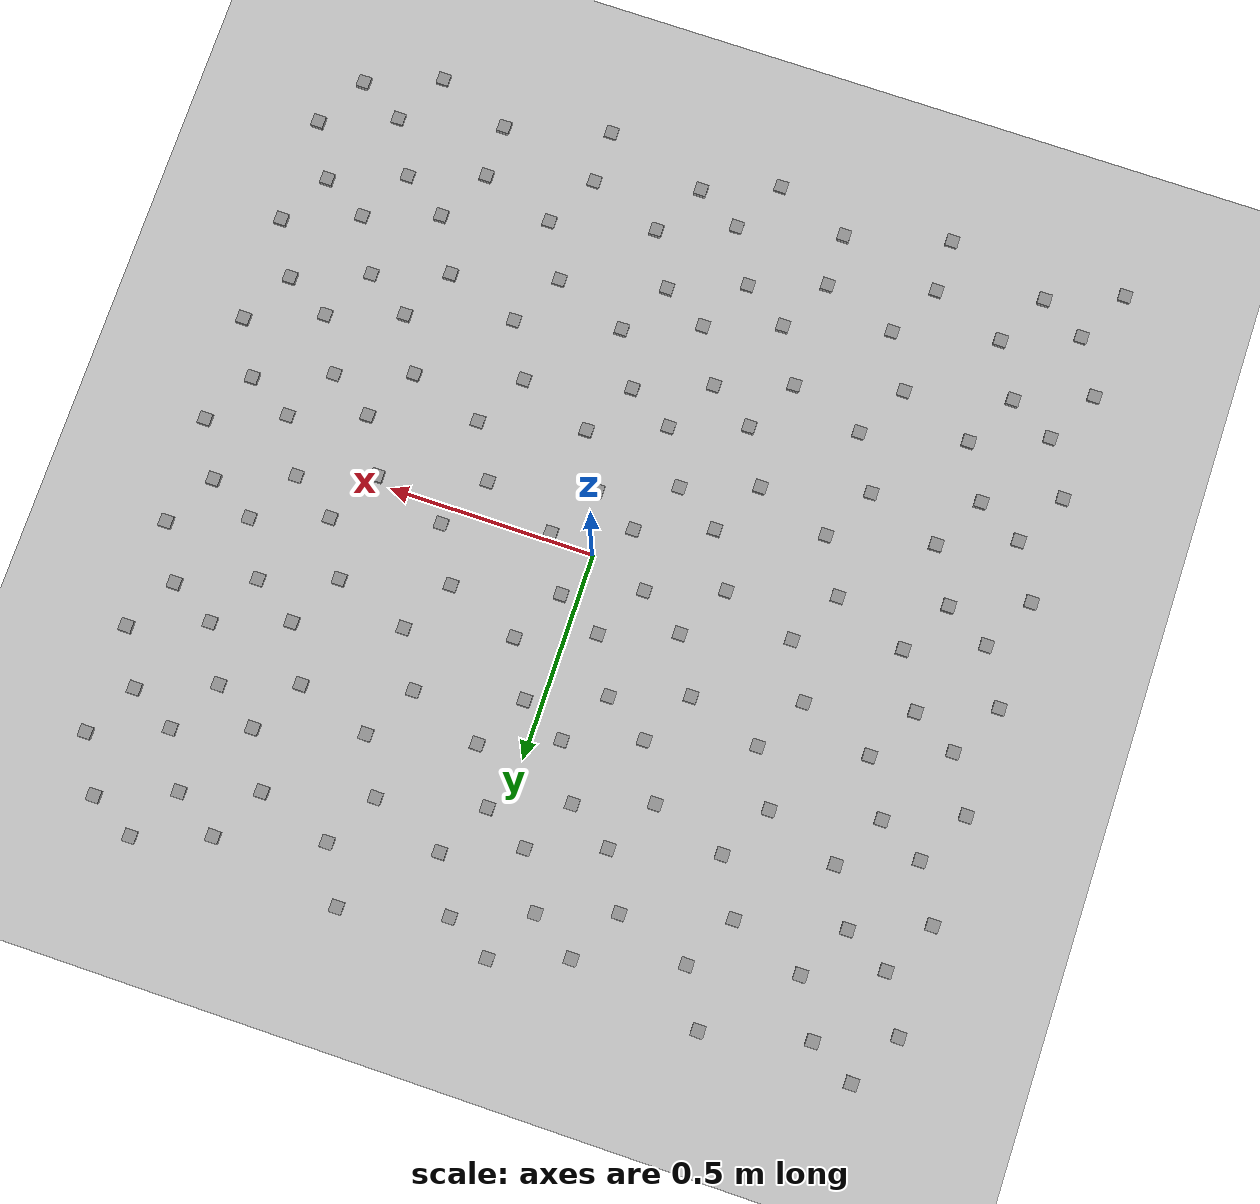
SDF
<?xml version="1.0" ?>
           <sdf version="1.5">
           <world name="default">
           <scene>
           <origin_visual>0</origin_visual>
           <grid>0</grid>
           </scene>
           <physics type="ode">
           <max_step_size>0.003</max_step_size>

           <!-- Run as fast as possible -->
           <real_time_update_rate>0.0</real_time_update_rate>
           <ode>
           <constraints>
           <!-- Simulator.cpp -->
           <erp>0.1</erp>
           <cfm>10e-6</cfm>

           <!-- Making this smaller seems to decrease rather than increase stability. -->
           <contact_max_correcting_vel>100</contact_max_correcting_vel>
           <contact_surface_layer>1e-8</contact_surface_layer>
           </constraints>
           <solver>
           <type>quick</type>
           </solver>
           </ode>
           </physics>
<model name='unit_box_0'>
                     <pose frame=''>-1 -1 0 0 0 0</pose>
                     <link name='link'>
                     <inertial>
                     <mass>1</mass>
                     <inertia>
                     <ixx>0</ixx>
                     <ixy>0</ixy>
                     <ixz>0</ixz>
                     <iyy>0</iyy>
                     <iyz>0</iyz>
                     <izz>0</izz>
                     </inertia>
                     </inertial>
                     <collision name='collision'>
                     <geometry>
                     <box>
                     <size>0.03 0.03 0.01</size>
                     </box>
                     </geometry>
                     <max_contacts>10</max_contacts>
                     <surface>
                     <contact>
                     <ode/>
                     </contact>
                     <bounce/>
                     <friction>
                     <ode/>
                     </friction>
                     </surface>
                     </collision>
                     <visual name='visual'>
                     <geometry>
                     <box>
                     <size>0.03 0.03 0.01</size>
                     </box>
                     </geometry>
                     <material>
                     <script>
                     <name>Gazebo/Grey</name>
                     <uri>file://media/materials/scripts/gazebo.material</uri>
                     </script>
                     </material>
                     </visual>
                     <self_collide>0</self_collide>
                     <kinematic>0</kinematic>
                     <gravity>1</gravity>
                     </link>
                     </model>
<model name='unit_box_1'>
                     <pose frame=''>-0.93 -0.87 0 0 0 0</pose>
                     <link name='link'>
                     <inertial>
                     <mass>1</mass>
                     <inertia>
                     <ixx>0</ixx>
                     <ixy>0</ixy>
                     <ixz>0</ixz>
                     <iyy>0</iyy>
                     <iyz>0</iyz>
                     <izz>0</izz>
                     </inertia>
                     </inertial>
                     <collision name='collision'>
                     <geometry>
                     <box>
                     <size>0.03 0.03 0.01</size>
                     </box>
                     </geometry>
                     <max_contacts>10</max_contacts>
                     <surface>
                     <contact>
                     <ode/>
                     </contact>
                     <bounce/>
                     <friction>
                     <ode/>
                     </friction>
                     </surface>
                     </collision>
                     <visual name='visual'>
                     <geometry>
                     <box>
                     <size>0.03 0.03 0.01</size>
                     </box>
                     </geometry>
                     <material>
                     <script>
                     <name>Gazebo/Grey</name>
                     <uri>file://media/materials/scripts/gazebo.material</uri>
                     </script>
                     </material>
                     </visual>
                     <self_collide>0</self_collide>
                     <kinematic>0</kinematic>
                     <gravity>1</gravity>
                     </link>
                     </model>
<model name='unit_box_2'>
                     <pose frame=''>-1 -0.74 0 0 0 0</pose>
                     <link name='link'>
                     <inertial>
                     <mass>1</mass>
                     <inertia>
                     <ixx>0</ixx>
                     <ixy>0</ixy>
                     <ixz>0</ixz>
                     <iyy>0</iyy>
                     <iyz>0</iyz>
                     <izz>0</izz>
                     </inertia>
                     </inertial>
                     <collision name='collision'>
                     <geometry>
                     <box>
                     <size>0.03 0.03 0.01</size>
                     </box>
                     </geometry>
                     <max_contacts>10</max_contacts>
                     <surface>
                     <contact>
                     <ode/>
                     </contact>
                     <bounce/>
                     <friction>
                     <ode/>
                     </friction>
                     </surface>
                     </collision>
                     <visual name='visual'>
                     <geometry>
                     <box>
                     <size>0.03 0.03 0.01</size>
                     </box>
                     </geometry>
                     <material>
                     <script>
                     <name>Gazebo/Grey</name>
                     <uri>file://media/materials/scripts/gazebo.material</uri>
                     </script>
                     </material>
                     </visual>
                     <self_collide>0</self_collide>
                     <kinematic>0</kinematic>
                     <gravity>1</gravity>
                     </link>
                     </model>
<model name='unit_box_3'>
                     <pose frame=''>-0.93 -0.61 0 0 0 0</pose>
                     <link name='link'>
                     <inertial>
                     <mass>1</mass>
                     <inertia>
                     <ixx>0</ixx>
                     <ixy>0</ixy>
                     <ixz>0</ixz>
                     <iyy>0</iyy>
                     <iyz>0</iyz>
                     <izz>0</izz>
                     </inertia>
                     </inertial>
                     <collision name='collision'>
                     <geometry>
                     <box>
                     <size>0.03 0.03 0.01</size>
                     </box>
                     </geometry>
                     <max_contacts>10</max_contacts>
                     <surface>
                     <contact>
                     <ode/>
                     </contact>
                     <bounce/>
                     <friction>
                     <ode/>
                     </friction>
                     </surface>
                     </collision>
                     <visual name='visual'>
                     <geometry>
                     <box>
                     <size>0.03 0.03 0.01</size>
                     </box>
                     </geometry>
                     <material>
                     <script>
                     <name>Gazebo/Grey</name>
                     <uri>file://media/materials/scripts/gazebo.material</uri>
                     </script>
                     </material>
                     </visual>
                     <self_collide>0</self_collide>
                     <kinematic>0</kinematic>
                     <gravity>1</gravity>
                     </link>
                     </model>
<model name='unit_box_4'>
                     <pose frame=''>-1 -0.48 0 0 0 0</pose>
                     <link name='link'>
                     <inertial>
                     <mass>1</mass>
                     <inertia>
                     <ixx>0</ixx>
                     <ixy>0</ixy>
                     <ixz>0</ixz>
                     <iyy>0</iyy>
                     <iyz>0</iyz>
                     <izz>0</izz>
                     </inertia>
                     </inertial>
                     <collision name='collision'>
                     <geometry>
                     <box>
                     <size>0.03 0.03 0.01</size>
                     </box>
                     </geometry>
                     <max_contacts>10</max_contacts>
                     <surface>
                     <contact>
                     <ode/>
                     </contact>
                     <bounce/>
                     <friction>
                     <ode/>
                     </friction>
                     </surface>
                     </collision>
                     <visual name='visual'>
                     <geometry>
                     <box>
                     <size>0.03 0.03 0.01</size>
                     </box>
                     </geometry>
                     <material>
                     <script>
                     <name>Gazebo/Grey</name>
                     <uri>file://media/materials/scripts/gazebo.material</uri>
                     </script>
                     </material>
                     </visual>
                     <self_collide>0</self_collide>
                     <kinematic>0</kinematic>
                     <gravity>1</gravity>
                     </link>
                     </model>
<model name='unit_box_5'>
                     <pose frame=''>-0.93 -0.35 0 0 0 0</pose>
                     <link name='link'>
                     <inertial>
                     <mass>1</mass>
                     <inertia>
                     <ixx>0</ixx>
                     <ixy>0</ixy>
                     <ixz>0</ixz>
                     <iyy>0</iyy>
                     <iyz>0</iyz>
                     <izz>0</izz>
                     </inertia>
                     </inertial>
                     <collision name='collision'>
                     <geometry>
                     <box>
                     <size>0.03 0.03 0.01</size>
                     </box>
                     </geometry>
                     <max_contacts>10</max_contacts>
                     <surface>
                     <contact>
                     <ode/>
                     </contact>
                     <bounce/>
                     <friction>
                     <ode/>
                     </friction>
                     </surface>
                     </collision>
                     <visual name='visual'>
                     <geometry>
                     <box>
                     <size>0.03 0.03 0.01</size>
                     </box>
                     </geometry>
                     <material>
                     <script>
                     <name>Gazebo/Grey</name>
                     <uri>file://media/materials/scripts/gazebo.material</uri>
                     </script>
                     </material>
                     </visual>
                     <self_collide>0</self_collide>
                     <kinematic>0</kinematic>
                     <gravity>1</gravity>
                     </link>
                     </model>
<model name='unit_box_6'>
                     <pose frame=''>-1 -0.22 0 0 0 0</pose>
                     <link name='link'>
                     <inertial>
                     <mass>1</mass>
                     <inertia>
                     <ixx>0</ixx>
                     <ixy>0</ixy>
                     <ixz>0</ixz>
                     <iyy>0</iyy>
                     <iyz>0</iyz>
                     <izz>0</izz>
                     </inertia>
                     </inertial>
                     <collision name='collision'>
                     <geometry>
                     <box>
                     <size>0.03 0.03 0.01</size>
                     </box>
                     </geometry>
                     <max_contacts>10</max_contacts>
                     <surface>
                     <contact>
                     <ode/>
                     </contact>
                     <bounce/>
                     <friction>
                     <ode/>
                     </friction>
                     </surface>
                     </collision>
                     <visual name='visual'>
                     <geometry>
                     <box>
                     <size>0.03 0.03 0.01</size>
                     </box>
                     </geometry>
                     <material>
                     <script>
                     <name>Gazebo/Grey</name>
                     <uri>file://media/materials/scripts/gazebo.material</uri>
                     </script>
                     </material>
                     </visual>
                     <self_collide>0</self_collide>
                     <kinematic>0</kinematic>
                     <gravity>1</gravity>
                     </link>
                     </model>
<model name='unit_box_7'>
                     <pose frame=''>-0.93 -0.0899999999999999 0 0 0 0</pose>
                     <link name='link'>
                     <inertial>
                     <mass>1</mass>
                     <inertia>
                     <ixx>0</ixx>
                     <ixy>0</ixy>
                     <ixz>0</ixz>
                     <iyy>0</iyy>
                     <iyz>0</iyz>
                     <izz>0</izz>
                     </inertia>
                     </inertial>
                     <collision name='collision'>
                     <geometry>
                     <box>
                     <size>0.03 0.03 0.01</size>
                     </box>
                     </geometry>
                     <max_contacts>10</max_contacts>
                     <surface>
                     <contact>
                     <ode/>
                     </contact>
                     <bounce/>
                     <friction>
                     <ode/>
                     </friction>
                     </surface>
                     </collision>
                     <visual name='visual'>
                     <geometry>
                     <box>
                     <size>0.03 0.03 0.01</size>
                     </box>
                     </geometry>
                     <material>
                     <script>
                     <name>Gazebo/Grey</name>
                     <uri>file://media/materials/scripts/gazebo.material</uri>
                     </script>
                     </material>
                     </visual>
                     <self_collide>0</self_collide>
                     <kinematic>0</kinematic>
                     <gravity>1</gravity>
                     </link>
                     </model>
<model name='unit_box_8'>
                     <pose frame=''>-1 0.0400000000000001 0 0 0 0</pose>
                     <link name='link'>
                     <inertial>
                     <mass>1</mass>
                     <inertia>
                     <ixx>0</ixx>
                     <ixy>0</ixy>
                     <ixz>0</ixz>
                     <iyy>0</iyy>
                     <iyz>0</iyz>
                     <izz>0</izz>
                     </inertia>
                     </inertial>
                     <collision name='collision'>
                     <geometry>
                     <box>
                     <size>0.03 0.03 0.01</size>
                     </box>
                     </geometry>
                     <max_contacts>10</max_contacts>
                     <surface>
                     <contact>
                     <ode/>
                     </contact>
                     <bounce/>
                     <friction>
                     <ode/>
                     </friction>
                     </surface>
                     </collision>
                     <visual name='visual'>
                     <geometry>
                     <box>
                     <size>0.03 0.03 0.01</size>
                     </box>
                     </geometry>
                     <material>
                     <script>
                     <name>Gazebo/Grey</name>
                     <uri>file://media/materials/scripts/gazebo.material</uri>
                     </script>
                     </material>
                     </visual>
                     <self_collide>0</self_collide>
                     <kinematic>0</kinematic>
                     <gravity>1</gravity>
                     </link>
                     </model>
<model name='unit_box_9'>
                     <pose frame=''>-0.93 0.17 0 0 0 0</pose>
                     <link name='link'>
                     <inertial>
                     <mass>1</mass>
                     <inertia>
                     <ixx>0</ixx>
                     <ixy>0</ixy>
                     <ixz>0</ixz>
                     <iyy>0</iyy>
                     <iyz>0</iyz>
                     <izz>0</izz>
                     </inertia>
                     </inertial>
                     <collision name='collision'>
                     <geometry>
                     <box>
                     <size>0.03 0.03 0.01</size>
                     </box>
                     </geometry>
                     <max_contacts>10</max_contacts>
                     <surface>
                     <contact>
                     <ode/>
                     </contact>
                     <bounce/>
                     <friction>
                     <ode/>
                     </friction>
                     </surface>
                     </collision>
                     <visual name='visual'>
                     <geometry>
                     <box>
                     <size>0.03 0.03 0.01</size>
                     </box>
                     </geometry>
                     <material>
                     <script>
                     <name>Gazebo/Grey</name>
                     <uri>file://media/materials/scripts/gazebo.material</uri>
                     </script>
                     </material>
                     </visual>
                     <self_collide>0</self_collide>
                     <kinematic>0</kinematic>
                     <gravity>1</gravity>
                     </link>
                     </model>
<model name='unit_box_10'>
                     <pose frame=''>-1 0.3 0 0 0 0</pose>
                     <link name='link'>
                     <inertial>
                     <mass>1</mass>
                     <inertia>
                     <ixx>0</ixx>
                     <ixy>0</ixy>
                     <ixz>0</ixz>
                     <iyy>0</iyy>
                     <iyz>0</iyz>
                     <izz>0</izz>
                     </inertia>
                     </inertial>
                     <collision name='collision'>
                     <geometry>
                     <box>
                     <size>0.03 0.03 0.01</size>
                     </box>
                     </geometry>
                     <max_contacts>10</max_contacts>
                     <surface>
                     <contact>
                     <ode/>
                     </contact>
                     <bounce/>
                     <friction>
                     <ode/>
                     </friction>
                     </surface>
                     </collision>
                     <visual name='visual'>
                     <geometry>
                     <box>
                     <size>0.03 0.03 0.01</size>
                     </box>
                     </geometry>
                     <material>
                     <script>
                     <name>Gazebo/Grey</name>
                     <uri>file://media/materials/scripts/gazebo.material</uri>
                     </script>
                     </material>
                     </visual>
                     <self_collide>0</self_collide>
                     <kinematic>0</kinematic>
                     <gravity>1</gravity>
                     </link>
                     </model>
<model name='unit_box_11'>
                     <pose frame=''>-0.93 0.43 0 0 0 0</pose>
                     <link name='link'>
                     <inertial>
                     <mass>1</mass>
                     <inertia>
                     <ixx>0</ixx>
                     <ixy>0</ixy>
                     <ixz>0</ixz>
                     <iyy>0</iyy>
                     <iyz>0</iyz>
                     <izz>0</izz>
                     </inertia>
                     </inertial>
                     <collision name='collision'>
                     <geometry>
                     <box>
                     <size>0.03 0.03 0.01</size>
                     </box>
                     </geometry>
                     <max_contacts>10</max_contacts>
                     <surface>
                     <contact>
                     <ode/>
                     </contact>
                     <bounce/>
                     <friction>
                     <ode/>
                     </friction>
                     </surface>
                     </collision>
                     <visual name='visual'>
                     <geometry>
                     <box>
                     <size>0.03 0.03 0.01</size>
                     </box>
                     </geometry>
                     <material>
                     <script>
                     <name>Gazebo/Grey</name>
                     <uri>file://media/materials/scripts/gazebo.material</uri>
                     </script>
                     </material>
                     </visual>
                     <self_collide>0</self_collide>
                     <kinematic>0</kinematic>
                     <gravity>1</gravity>
                     </link>
                     </model>
<model name='unit_box_12'>
                     <pose frame=''>-1 0.56 0 0 0 0</pose>
                     <link name='link'>
                     <inertial>
                     <mass>1</mass>
                     <inertia>
                     <ixx>0</ixx>
                     <ixy>0</ixy>
                     <ixz>0</ixz>
                     <iyy>0</iyy>
                     <iyz>0</iyz>
                     <izz>0</izz>
                     </inertia>
                     </inertial>
                     <collision name='collision'>
                     <geometry>
                     <box>
                     <size>0.03 0.03 0.01</size>
                     </box>
                     </geometry>
                     <max_contacts>10</max_contacts>
                     <surface>
                     <contact>
                     <ode/>
                     </contact>
                     <bounce/>
                     <friction>
                     <ode/>
                     </friction>
                     </surface>
                     </collision>
                     <visual name='visual'>
                     <geometry>
                     <box>
                     <size>0.03 0.03 0.01</size>
                     </box>
                     </geometry>
                     <material>
                     <script>
                     <name>Gazebo/Grey</name>
                     <uri>file://media/materials/scripts/gazebo.material</uri>
                     </script>
                     </material>
                     </visual>
                     <self_collide>0</self_collide>
                     <kinematic>0</kinematic>
                     <gravity>1</gravity>
                     </link>
                     </model>
<model name='unit_box_13'>
                     <pose frame=''>-0.93 0.69 0 0 0 0</pose>
                     <link name='link'>
                     <inertial>
                     <mass>1</mass>
                     <inertia>
                     <ixx>0</ixx>
                     <ixy>0</ixy>
                     <ixz>0</ixz>
                     <iyy>0</iyy>
                     <iyz>0</iyz>
                     <izz>0</izz>
                     </inertia>
                     </inertial>
                     <collision name='collision'>
                     <geometry>
                     <box>
                     <size>0.03 0.03 0.01</size>
                     </box>
                     </geometry>
                     <max_contacts>10</max_contacts>
                     <surface>
                     <contact>
                     <ode/>
                     </contact>
                     <bounce/>
                     <friction>
                     <ode/>
                     </friction>
                     </surface>
                     </collision>
                     <visual name='visual'>
                     <geometry>
                     <box>
                     <size>0.03 0.03 0.01</size>
                     </box>
                     </geometry>
                     <material>
                     <script>
                     <name>Gazebo/Grey</name>
                     <uri>file://media/materials/scripts/gazebo.material</uri>
                     </script>
                     </material>
                     </visual>
                     <self_collide>0</self_collide>
                     <kinematic>0</kinematic>
                     <gravity>1</gravity>
                     </link>
                     </model>
<model name='unit_box_14'>
                     <pose frame=''>-1 0.82 0 0 0 0</pose>
                     <link name='link'>
                     <inertial>
                     <mass>1</mass>
                     <inertia>
                     <ixx>0</ixx>
                     <ixy>0</ixy>
                     <ixz>0</ixz>
                     <iyy>0</iyy>
                     <iyz>0</iyz>
                     <izz>0</izz>
                     </inertia>
                     </inertial>
                     <collision name='collision'>
                     <geometry>
                     <box>
                     <size>0.03 0.03 0.01</size>
                     </box>
                     </geometry>
                     <max_contacts>10</max_contacts>
                     <surface>
                     <contact>
                     <ode/>
                     </contact>
                     <bounce/>
                     <friction>
                     <ode/>
                     </friction>
                     </surface>
                     </collision>
                     <visual name='visual'>
                     <geometry>
                     <box>
                     <size>0.03 0.03 0.01</size>
                     </box>
                     </geometry>
                     <material>
                     <script>
                     <name>Gazebo/Grey</name>
                     <uri>file://media/materials/scripts/gazebo.material</uri>
                     </script>
                     </material>
                     </visual>
                     <self_collide>0</self_collide>
                     <kinematic>0</kinematic>
                     <gravity>1</gravity>
                     </link>
                     </model>
<model name='unit_box_15'>
                     <pose frame=''>-0.93 0.95 0 0 0 0</pose>
                     <link name='link'>
                     <inertial>
                     <mass>1</mass>
                     <inertia>
                     <ixx>0</ixx>
                     <ixy>0</ixy>
                     <ixz>0</ixz>
                     <iyy>0</iyy>
                     <iyz>0</iyz>
                     <izz>0</izz>
                     </inertia>
                     </inertial>
                     <collision name='collision'>
                     <geometry>
                     <box>
                     <size>0.03 0.03 0.01</size>
                     </box>
                     </geometry>
                     <max_contacts>10</max_contacts>
                     <surface>
                     <contact>
                     <ode/>
                     </contact>
                     <bounce/>
                     <friction>
                     <ode/>
                     </friction>
                     </surface>
                     </collision>
                     <visual name='visual'>
                     <geometry>
                     <box>
                     <size>0.03 0.03 0.01</size>
                     </box>
                     </geometry>
                     <material>
                     <script>
                     <name>Gazebo/Grey</name>
                     <uri>file://media/materials/scripts/gazebo.material</uri>
                     </script>
                     </material>
                     </visual>
                     <self_collide>0</self_collide>
                     <kinematic>0</kinematic>
                     <gravity>1</gravity>
                     </link>
                     </model>
<model name='unit_box_16'>
                     <pose frame=''>-0.82 -0.93 0 0 0 0</pose>
                     <link name='link'>
                     <inertial>
                     <mass>1</mass>
                     <inertia>
                     <ixx>0</ixx>
                     <ixy>0</ixy>
                     <ixz>0</ixz>
                     <iyy>0</iyy>
                     <iyz>0</iyz>
                     <izz>0</izz>
                     </inertia>
                     </inertial>
                     <collision name='collision'>
                     <geometry>
                     <box>
                     <size>0.03 0.03 0.02</size>
                     </box>
                     </geometry>
                     <max_contacts>10</max_contacts>
                     <surface>
                     <contact>
                     <ode/>
                     </contact>
                     <bounce/>
                     <friction>
                     <ode/>
                     </friction>
                     </surface>
                     </collision>
                     <visual name='visual'>
                     <geometry>
                     <box>
                     <size>0.03 0.03 0.02</size>
                     </box>
                     </geometry>
                     <material>
                     <script>
                     <name>Gazebo/Grey</name>
                     <uri>file://media/materials/scripts/gazebo.material</uri>
                     </script>
                     </material>
                     </visual>
                     <self_collide>0</self_collide>
                     <kinematic>0</kinematic>
                     <gravity>1</gravity>
                     </link>
                     </model>
<model name='unit_box_17'>
                     <pose frame=''>-0.75 -0.8 0 0 0 0</pose>
                     <link name='link'>
                     <inertial>
                     <mass>1</mass>
                     <inertia>
                     <ixx>0</ixx>
                     <ixy>0</ixy>
                     <ixz>0</ixz>
                     <iyy>0</iyy>
                     <iyz>0</iyz>
                     <izz>0</izz>
                     </inertia>
                     </inertial>
                     <collision name='collision'>
                     <geometry>
                     <box>
                     <size>0.03 0.03 0.02</size>
                     </box>
                     </geometry>
                     <max_contacts>10</max_contacts>
                     <surface>
                     <contact>
                     <ode/>
                     </contact>
                     <bounce/>
                     <friction>
                     <ode/>
                     </friction>
                     </surface>
                     </collision>
                     <visual name='visual'>
                     <geometry>
                     <box>
                     <size>0.03 0.03 0.02</size>
                     </box>
                     </geometry>
                     <material>
                     <script>
                     <name>Gazebo/Grey</name>
                     <uri>file://media/materials/scripts/gazebo.material</uri>
                     </script>
                     </material>
                     </visual>
                     <self_collide>0</self_collide>
                     <kinematic>0</kinematic>
                     <gravity>1</gravity>
                     </link>
                     </model>
<model name='unit_box_18'>
                     <pose frame=''>-0.82 -0.67 0 0 0 0</pose>
                     <link name='link'>
                     <inertial>
                     <mass>1</mass>
                     <inertia>
                     <ixx>0</ixx>
                     <ixy>0</ixy>
                     <ixz>0</ixz>
                     <iyy>0</iyy>
                     <iyz>0</iyz>
                     <izz>0</izz>
                     </inertia>
                     </inertial>
                     <collision name='collision'>
                     <geometry>
                     <box>
                     <size>0.03 0.03 0.02</size>
                     </box>
                     </geometry>
                     <max_contacts>10</max_contacts>
                     <surface>
                     <contact>
                     <ode/>
                     </contact>
                     <bounce/>
                     <friction>
                     <ode/>
                     </friction>
                     </surface>
                     </collision>
                     <visual name='visual'>
                     <geometry>
                     <box>
                     <size>0.03 0.03 0.02</size>
                     </box>
                     </geometry>
                     <material>
                     <script>
                     <name>Gazebo/Grey</name>
                     <uri>file://media/materials/scripts/gazebo.material</uri>
                     </script>
                     </material>
                     </visual>
                     <self_collide>0</self_collide>
                     <kinematic>0</kinematic>
                     <gravity>1</gravity>
                     </link>
                     </model>
<model name='unit_box_19'>
                     <pose frame=''>-0.75 -0.54 0 0 0 0</pose>
                     <link name='link'>
                     <inertial>
                     <mass>1</mass>
                     <inertia>
                     <ixx>0</ixx>
                     <ixy>0</ixy>
                     <ixz>0</ixz>
                     <iyy>0</iyy>
                     <iyz>0</iyz>
                     <izz>0</izz>
                     </inertia>
                     </inertial>
                     <collision name='collision'>
                     <geometry>
                     <box>
                     <size>0.03 0.03 0.02</size>
                     </box>
                     </geometry>
                     <max_contacts>10</max_contacts>
                     <surface>
                     <contact>
                     <ode/>
                     </contact>
                     <bounce/>
                     <friction>
                     <ode/>
                     </friction>
                     </surface>
                     </collision>
                     <visual name='visual'>
                     <geometry>
                     <box>
                     <size>0.03 0.03 0.02</size>
                     </box>
                     </geometry>
                     <material>
                     <script>
                     <name>Gazebo/Grey</name>
                     <uri>file://media/materials/scripts/gazebo.material</uri>
                     </script>
                     </material>
                     </visual>
                     <self_collide>0</self_collide>
                     <kinematic>0</kinematic>
                     <gravity>1</gravity>
                     </link>
                     </model>
<model name='unit_box_20'>
                     <pose frame=''>-0.82 -0.41 0 0 0 0</pose>
                     <link name='link'>
                     <inertial>
                     <mass>1</mass>
                     <inertia>
                     <ixx>0</ixx>
                     <ixy>0</ixy>
                     <ixz>0</ixz>
                     <iyy>0</iyy>
                     <iyz>0</iyz>
                     <izz>0</izz>
                     </inertia>
                     </inertial>
                     <collision name='collision'>
                     <geometry>
                     <box>
                     <size>0.03 0.03 0.02</size>
                     </box>
                     </geometry>
                     <max_contacts>10</max_contacts>
                     <surface>
                     <contact>
                     <ode/>
                     </contact>
                     <bounce/>
                     <friction>
                     <ode/>
                     </friction>
                     </surface>
                     </collision>
                     <visual name='visual'>
                     <geometry>
                     <box>
                     <size>0.03 0.03 0.02</size>
                     </box>
                     </geometry>
                     <material>
                     <script>
                     <name>Gazebo/Grey</name>
                     <uri>file://media/materials/scripts/gazebo.material</uri>
                     </script>
                     </material>
                     </visual>
                     <self_collide>0</self_collide>
                     <kinematic>0</kinematic>
                     <gravity>1</gravity>
                     </link>
                     </model>
<model name='unit_box_21'>
                     <pose frame=''>-0.75 -0.28 0 0 0 0</pose>
                     <link name='link'>
                     <inertial>
                     <mass>1</mass>
                     <inertia>
                     <ixx>0</ixx>
                     <ixy>0</ixy>
                     <ixz>0</ixz>
                     <iyy>0</iyy>
                     <iyz>0</iyz>
                     <izz>0</izz>
                     </inertia>
                     </inertial>
                     <collision name='collision'>
                     <geometry>
                     <box>
                     <size>0.03 0.03 0.02</size>
                     </box>
                     </geometry>
                     <max_contacts>10</max_contacts>
                     <surface>
                     <contact>
                     <ode/>
                     </contact>
                     <bounce/>
                     <friction>
                     <ode/>
                     </friction>
                     </surface>
                     </collision>
                     <visual name='visual'>
                     <geometry>
                     <box>
                     <size>0.03 0.03 0.02</size>
                     </box>
                     </geometry>
                     <material>
                     <script>
                     <name>Gazebo/Grey</name>
                     <uri>file://media/materials/scripts/gazebo.material</uri>
                     </script>
                     </material>
                     </visual>
                     <self_collide>0</self_collide>
                     <kinematic>0</kinematic>
                     <gravity>1</gravity>
                     </link>
                     </model>
<model name='unit_box_22'>
                     <pose frame=''>-0.82 -0.15 0 0 0 0</pose>
                     <link name='link'>
                     <inertial>
                     <mass>1</mass>
                     <inertia>
                     <ixx>0</ixx>
                     <ixy>0</ixy>
                     <ixz>0</ixz>
                     <iyy>0</iyy>
                     <iyz>0</iyz>
                     <izz>0</izz>
                     </inertia>
                     </inertial>
                     <collision name='collision'>
                     <geometry>
                     <box>
                     <size>0.03 0.03 0.02</size>
                     </box>
                     </geometry>
                     <max_contacts>10</max_contacts>
                     <surface>
                     <contact>
                     <ode/>
                     </contact>
                     <bounce/>
                     <friction>
                     <ode/>
                     </friction>
                     </surface>
                     </collision>
                     <visual name='visual'>
                     <geometry>
                     <box>
                     <size>0.03 0.03 0.02</size>
                     </box>
                     </geometry>
                     <material>
                     <script>
                     <name>Gazebo/Grey</name>
                     <uri>file://media/materials/scripts/gazebo.material</uri>
                     </script>
                     </material>
                     </visual>
                     <self_collide>0</self_collide>
                     <kinematic>0</kinematic>
                     <gravity>1</gravity>
                     </link>
                     </model>
<model name='unit_box_23'>
                     <pose frame=''>-0.75 -0.02 0 0 0 0</pose>
                     <link name='link'>
                     <inertial>
                     <mass>1</mass>
                     <inertia>
                     <ixx>0</ixx>
                     <ixy>0</ixy>
                     <ixz>0</ixz>
                     <iyy>0</iyy>
                     <iyz>0</iyz>
                     <izz>0</izz>
                     </inertia>
                     </inertial>
                     <collision name='collision'>
                     <geometry>
                     <box>
                     <size>0.03 0.03 0.02</size>
                     </box>
                     </geometry>
                     <max_contacts>10</max_contacts>
                     <surface>
                     <contact>
                     <ode/>
                     </contact>
                     <bounce/>
                     <friction>
                     <ode/>
                     </friction>
                     </surface>
                     </collision>
                     <visual name='visual'>
                     <geometry>
                     <box>
                     <size>0.03 0.03 0.02</size>
                     </box>
                     </geometry>
                     <material>
                     <script>
                     <name>Gazebo/Grey</name>
                     <uri>file://media/materials/scripts/gazebo.material</uri>
                     </script>
                     </material>
                     </visual>
                     <self_collide>0</self_collide>
                     <kinematic>0</kinematic>
                     <gravity>1</gravity>
                     </link>
                     </model>
<model name='unit_box_24'>
                     <pose frame=''>-0.82 0.11 0 0 0 0</pose>
                     <link name='link'>
                     <inertial>
                     <mass>1</mass>
                     <inertia>
                     <ixx>0</ixx>
                     <ixy>0</ixy>
                     <ixz>0</ixz>
                     <iyy>0</iyy>
                     <iyz>0</iyz>
                     <izz>0</izz>
                     </inertia>
                     </inertial>
                     <collision name='collision'>
                     <geometry>
                     <box>
                     <size>0.03 0.03 0.02</size>
                     </box>
                     </geometry>
                     <max_contacts>10</max_contacts>
                     <surface>
                     <contact>
                     <ode/>
                     </contact>
                     <bounce/>
                     <friction>
                     <ode/>
                     </friction>
                     </surface>
                     </collision>
                     <visual name='visual'>
                     <geometry>
                     <box>
                     <size>0.03 0.03 0.02</size>
                     </box>
                     </geometry>
                     <material>
                     <script>
                     <name>Gazebo/Grey</name>
                     <uri>file://media/materials/scripts/gazebo.material</uri>
                     </script>
                     </material>
                     </visual>
                     <self_collide>0</self_collide>
                     <kinematic>0</kinematic>
                     <gravity>1</gravity>
                     </link>
                     </model>
<model name='unit_box_25'>
                     <pose frame=''>-0.75 0.24 0 0 0 0</pose>
                     <link name='link'>
                     <inertial>
                     <mass>1</mass>
                     <inertia>
                     <ixx>0</ixx>
                     <ixy>0</ixy>
                     <ixz>0</ixz>
                     <iyy>0</iyy>
                     <iyz>0</iyz>
                     <izz>0</izz>
                     </inertia>
                     </inertial>
                     <collision name='collision'>
                     <geometry>
                     <box>
                     <size>0.03 0.03 0.02</size>
                     </box>
                     </geometry>
                     <max_contacts>10</max_contacts>
                     <surface>
                     <contact>
                     <ode/>
                     </contact>
                     <bounce/>
                     <friction>
                     <ode/>
                     </friction>
                     </surface>
                     </collision>
                     <visual name='visual'>
                     <geometry>
                     <box>
                     <size>0.03 0.03 0.02</size>
                     </box>
                     </geometry>
                     <material>
                     <script>
                     <name>Gazebo/Grey</name>
                     <uri>file://media/materials/scripts/gazebo.material</uri>
                     </script>
                     </material>
                     </visual>
                     <self_collide>0</self_collide>
                     <kinematic>0</kinematic>
                     <gravity>1</gravity>
                     </link>
                     </model>
<model name='unit_box_26'>
                     <pose frame=''>-0.82 0.37 0 0 0 0</pose>
                     <link name='link'>
                     <inertial>
                     <mass>1</mass>
                     <inertia>
                     <ixx>0</ixx>
                     <ixy>0</ixy>
                     <ixz>0</ixz>
                     <iyy>0</iyy>
                     <iyz>0</iyz>
                     <izz>0</izz>
                     </inertia>
                     </inertial>
                     <collision name='collision'>
                     <geometry>
                     <box>
                     <size>0.03 0.03 0.02</size>
                     </box>
                     </geometry>
                     <max_contacts>10</max_contacts>
                     <surface>
                     <contact>
                     <ode/>
                     </contact>
                     <bounce/>
                     <friction>
                     <ode/>
                     </friction>
                     </surface>
                     </collision>
                     <visual name='visual'>
                     <geometry>
                     <box>
                     <size>0.03 0.03 0.02</size>
                     </box>
                     </geometry>
                     <material>
                     <script>
                     <name>Gazebo/Grey</name>
                     <uri>file://media/materials/scripts/gazebo.material</uri>
                     </script>
                     </material>
                     </visual>
                     <self_collide>0</self_collide>
                     <kinematic>0</kinematic>
                     <gravity>1</gravity>
                     </link>
                     </model>
<model name='unit_box_27'>
                     <pose frame=''>-0.75 0.5 0 0 0 0</pose>
                     <link name='link'>
                     <inertial>
                     <mass>1</mass>
                     <inertia>
                     <ixx>0</ixx>
                     <ixy>0</ixy>
                     <ixz>0</ixz>
                     <iyy>0</iyy>
                     <iyz>0</iyz>
                     <izz>0</izz>
                     </inertia>
                     </inertial>
                     <collision name='collision'>
                     <geometry>
                     <box>
                     <size>0.03 0.03 0.02</size>
                     </box>
                     </geometry>
                     <max_contacts>10</max_contacts>
                     <surface>
                     <contact>
                     <ode/>
                     </contact>
                     <bounce/>
                     <friction>
                     <ode/>
                     </friction>
                     </surface>
                     </collision>
                     <visual name='visual'>
                     <geometry>
                     <box>
                     <size>0.03 0.03 0.02</size>
                     </box>
                     </geometry>
                     <material>
                     <script>
                     <name>Gazebo/Grey</name>
                     <uri>file://media/materials/scripts/gazebo.material</uri>
                     </script>
                     </material>
                     </visual>
                     <self_collide>0</self_collide>
                     <kinematic>0</kinematic>
                     <gravity>1</gravity>
                     </link>
                     </model>
<model name='unit_box_28'>
                     <pose frame=''>-0.82 0.63 0 0 0 0</pose>
                     <link name='link'>
                     <inertial>
                     <mass>1</mass>
                     <inertia>
                     <ixx>0</ixx>
                     <ixy>0</ixy>
                     <ixz>0</ixz>
                     <iyy>0</iyy>
                     <iyz>0</iyz>
                     <izz>0</izz>
                     </inertia>
                     </inertial>
                     <collision name='collision'>
                     <geometry>
                     <box>
                     <size>0.03 0.03 0.02</size>
                     </box>
                     </geometry>
                     <max_contacts>10</max_contacts>
                     <surface>
                     <contact>
                     <ode/>
                     </contact>
                     <bounce/>
                     <friction>
                     <ode/>
                     </friction>
                     </surface>
                     </collision>
                     <visual name='visual'>
                     <geometry>
                     <box>
                     <size>0.03 0.03 0.02</size>
                     </box>
                     </geometry>
                     <material>
                     <script>
                     <name>Gazebo/Grey</name>
                     <uri>file://media/materials/scripts/gazebo.material</uri>
                     </script>
                     </material>
                     </visual>
                     <self_collide>0</self_collide>
                     <kinematic>0</kinematic>
                     <gravity>1</gravity>
                     </link>
                     </model>
<model name='unit_box_29'>
                     <pose frame=''>-0.75 0.76 0 0 0 0</pose>
                     <link name='link'>
                     <inertial>
                     <mass>1</mass>
                     <inertia>
                     <ixx>0</ixx>
                     <ixy>0</ixy>
                     <ixz>0</ixz>
                     <iyy>0</iyy>
                     <iyz>0</iyz>
                     <izz>0</izz>
                     </inertia>
                     </inertial>
                     <collision name='collision'>
                     <geometry>
                     <box>
                     <size>0.03 0.03 0.02</size>
                     </box>
                     </geometry>
                     <max_contacts>10</max_contacts>
                     <surface>
                     <contact>
                     <ode/>
                     </contact>
                     <bounce/>
                     <friction>
                     <ode/>
                     </friction>
                     </surface>
                     </collision>
                     <visual name='visual'>
                     <geometry>
                     <box>
                     <size>0.03 0.03 0.02</size>
                     </box>
                     </geometry>
                     <material>
                     <script>
                     <name>Gazebo/Grey</name>
                     <uri>file://media/materials/scripts/gazebo.material</uri>
                     </script>
                     </material>
                     </visual>
                     <self_collide>0</self_collide>
                     <kinematic>0</kinematic>
                     <gravity>1</gravity>
                     </link>
                     </model>
<model name='unit_box_30'>
                     <pose frame=''>-0.82 0.89 0 0 0 0</pose>
                     <link name='link'>
                     <inertial>
                     <mass>1</mass>
                     <inertia>
                     <ixx>0</ixx>
                     <ixy>0</ixy>
                     <ixz>0</ixz>
                     <iyy>0</iyy>
                     <iyz>0</iyz>
                     <izz>0</izz>
                     </inertia>
                     </inertial>
                     <collision name='collision'>
                     <geometry>
                     <box>
                     <size>0.03 0.03 0.02</size>
                     </box>
                     </geometry>
                     <max_contacts>10</max_contacts>
                     <surface>
                     <contact>
                     <ode/>
                     </contact>
                     <bounce/>
                     <friction>
                     <ode/>
                     </friction>
                     </surface>
                     </collision>
                     <visual name='visual'>
                     <geometry>
                     <box>
                     <size>0.03 0.03 0.02</size>
                     </box>
                     </geometry>
                     <material>
                     <script>
                     <name>Gazebo/Grey</name>
                     <uri>file://media/materials/scripts/gazebo.material</uri>
                     </script>
                     </material>
                     </visual>
                     <self_collide>0</self_collide>
                     <kinematic>0</kinematic>
                     <gravity>1</gravity>
                     </link>
                     </model>
<model name='unit_box_31'>
                     <pose frame=''>-0.57 -1 0 0 0 0</pose>
                     <link name='link'>
                     <inertial>
                     <mass>1</mass>
                     <inertia>
                     <ixx>0</ixx>
                     <ixy>0</ixy>
                     <ixz>0</ixz>
                     <iyy>0</iyy>
                     <iyz>0</iyz>
                     <izz>0</izz>
                     </inertia>
                     </inertial>
                     <collision name='collision'>
                     <geometry>
                     <box>
                     <size>0.03 0.03 0.01</size>
                     </box>
                     </geometry>
                     <max_contacts>10</max_contacts>
                     <surface>
                     <contact>
                     <ode/>
                     </contact>
                     <bounce/>
                     <friction>
                     <ode/>
                     </friction>
                     </surface>
                     </collision>
                     <visual name='visual'>
                     <geometry>
                     <box>
                     <size>0.03 0.03 0.01</size>
                     </box>
                     </geometry>
                     <material>
                     <script>
                     <name>Gazebo/Grey</name>
                     <uri>file://media/materials/scripts/gazebo.material</uri>
                     </script>
                     </material>
                     </visual>
                     <self_collide>0</self_collide>
                     <kinematic>0</kinematic>
                     <gravity>1</gravity>
                     </link>
                     </model>
<model name='unit_box_32'>
                     <pose frame=''>-0.57 -0.87 0 0 0 0</pose>
                     <link name='link'>
                     <inertial>
                     <mass>1</mass>
                     <inertia>
                     <ixx>0</ixx>
                     <ixy>0</ixy>
                     <ixz>0</ixz>
                     <iyy>0</iyy>
                     <iyz>0</iyz>
                     <izz>0</izz>
                     </inertia>
                     </inertial>
                     <collision name='collision'>
                     <geometry>
                     <box>
                     <size>0.03 0.03 0.01</size>
                     </box>
                     </geometry>
                     <max_contacts>10</max_contacts>
                     <surface>
                     <contact>
                     <ode/>
                     </contact>
                     <bounce/>
                     <friction>
                     <ode/>
                     </friction>
                     </surface>
                     </collision>
                     <visual name='visual'>
                     <geometry>
                     <box>
                     <size>0.03 0.03 0.01</size>
                     </box>
                     </geometry>
                     <material>
                     <script>
                     <name>Gazebo/Grey</name>
                     <uri>file://media/materials/scripts/gazebo.material</uri>
                     </script>
                     </material>
                     </visual>
                     <self_collide>0</self_collide>
                     <kinematic>0</kinematic>
                     <gravity>1</gravity>
                     </link>
                     </model>
<model name='unit_box_33'>
                     <pose frame=''>-0.5 -0.74 0 0 0 0</pose>
                     <link name='link'>
                     <inertial>
                     <mass>1</mass>
                     <inertia>
                     <ixx>0</ixx>
                     <ixy>0</ixy>
                     <ixz>0</ixz>
                     <iyy>0</iyy>
                     <iyz>0</iyz>
                     <izz>0</izz>
                     </inertia>
                     </inertial>
                     <collision name='collision'>
                     <geometry>
                     <box>
                     <size>0.03 0.03 0.01</size>
                     </box>
                     </geometry>
                     <max_contacts>10</max_contacts>
                     <surface>
                     <contact>
                     <ode/>
                     </contact>
                     <bounce/>
                     <friction>
                     <ode/>
                     </friction>
                     </surface>
                     </collision>
                     <visual name='visual'>
                     <geometry>
                     <box>
                     <size>0.03 0.03 0.01</size>
                     </box>
                     </geometry>
                     <material>
                     <script>
                     <name>Gazebo/Grey</name>
                     <uri>file://media/materials/scripts/gazebo.material</uri>
                     </script>
                     </material>
                     </visual>
                     <self_collide>0</self_collide>
                     <kinematic>0</kinematic>
                     <gravity>1</gravity>
                     </link>
                     </model>
<model name='unit_box_34'>
                     <pose frame=''>-0.57 -0.61 0 0 0 0</pose>
                     <link name='link'>
                     <inertial>
                     <mass>1</mass>
                     <inertia>
                     <ixx>0</ixx>
                     <ixy>0</ixy>
                     <ixz>0</ixz>
                     <iyy>0</iyy>
                     <iyz>0</iyz>
                     <izz>0</izz>
                     </inertia>
                     </inertial>
                     <collision name='collision'>
                     <geometry>
                     <box>
                     <size>0.03 0.03 0.01</size>
                     </box>
                     </geometry>
                     <max_contacts>10</max_contacts>
                     <surface>
                     <contact>
                     <ode/>
                     </contact>
                     <bounce/>
                     <friction>
                     <ode/>
                     </friction>
                     </surface>
                     </collision>
                     <visual name='visual'>
                     <geometry>
                     <box>
                     <size>0.03 0.03 0.01</size>
                     </box>
                     </geometry>
                     <material>
                     <script>
                     <name>Gazebo/Grey</name>
                     <uri>file://media/materials/scripts/gazebo.material</uri>
                     </script>
                     </material>
                     </visual>
                     <self_collide>0</self_collide>
                     <kinematic>0</kinematic>
                     <gravity>1</gravity>
                     </link>
                     </model>
<model name='unit_box_35'>
                     <pose frame=''>-0.5 -0.48 0 0 0 0</pose>
                     <link name='link'>
                     <inertial>
                     <mass>1</mass>
                     <inertia>
                     <ixx>0</ixx>
                     <ixy>0</ixy>
                     <ixz>0</ixz>
                     <iyy>0</iyy>
                     <iyz>0</iyz>
                     <izz>0</izz>
                     </inertia>
                     </inertial>
                     <collision name='collision'>
                     <geometry>
                     <box>
                     <size>0.03 0.03 0.01</size>
                     </box>
                     </geometry>
                     <max_contacts>10</max_contacts>
                     <surface>
                     <contact>
                     <ode/>
                     </contact>
                     <bounce/>
                     <friction>
                     <ode/>
                     </friction>
                     </surface>
                     </collision>
                     <visual name='visual'>
                     <geometry>
                     <box>
                     <size>0.03 0.03 0.01</size>
                     </box>
                     </geometry>
                     <material>
                     <script>
                     <name>Gazebo/Grey</name>
                     <uri>file://media/materials/scripts/gazebo.material</uri>
                     </script>
                     </material>
                     </visual>
                     <self_collide>0</self_collide>
                     <kinematic>0</kinematic>
                     <gravity>1</gravity>
                     </link>
                     </model>
<model name='unit_box_36'>
                     <pose frame=''>-0.57 -0.35 0 0 0 0</pose>
                     <link name='link'>
                     <inertial>
                     <mass>1</mass>
                     <inertia>
                     <ixx>0</ixx>
                     <ixy>0</ixy>
                     <ixz>0</ixz>
                     <iyy>0</iyy>
                     <iyz>0</iyz>
                     <izz>0</izz>
                     </inertia>
                     </inertial>
                     <collision name='collision'>
                     <geometry>
                     <box>
                     <size>0.03 0.03 0.01</size>
                     </box>
                     </geometry>
                     <max_contacts>10</max_contacts>
                     <surface>
                     <contact>
                     <ode/>
                     </contact>
                     <bounce/>
                     <friction>
                     <ode/>
                     </friction>
                     </surface>
                     </collision>
                     <visual name='visual'>
                     <geometry>
                     <box>
                     <size>0.03 0.03 0.01</size>
                     </box>
                     </geometry>
                     <material>
                     <script>
                     <name>Gazebo/Grey</name>
                     <uri>file://media/materials/scripts/gazebo.material</uri>
                     </script>
                     </material>
                     </visual>
                     <self_collide>0</self_collide>
                     <kinematic>0</kinematic>
                     <gravity>1</gravity>
                     </link>
                     </model>
<model name='unit_box_37'>
                     <pose frame=''>-0.5 -0.22 0 0 0 0</pose>
                     <link name='link'>
                     <inertial>
                     <mass>1</mass>
                     <inertia>
                     <ixx>0</ixx>
                     <ixy>0</ixy>
                     <ixz>0</ixz>
                     <iyy>0</iyy>
                     <iyz>0</iyz>
                     <izz>0</izz>
                     </inertia>
                     </inertial>
                     <collision name='collision'>
                     <geometry>
                     <box>
                     <size>0.03 0.03 0.01</size>
                     </box>
                     </geometry>
                     <max_contacts>10</max_contacts>
                     <surface>
                     <contact>
                     <ode/>
                     </contact>
                     <bounce/>
                     <friction>
                     <ode/>
                     </friction>
                     </surface>
                     </collision>
                     <visual name='visual'>
                     <geometry>
                     <box>
                     <size>0.03 0.03 0.01</size>
                     </box>
                     </geometry>
                     <material>
                     <script>
                     <name>Gazebo/Grey</name>
                     <uri>file://media/materials/scripts/gazebo.material</uri>
                     </script>
                     </material>
                     </visual>
                     <self_collide>0</self_collide>
                     <kinematic>0</kinematic>
                     <gravity>1</gravity>
                     </link>
                     </model>
<model name='unit_box_38'>
                     <pose frame=''>-0.57 -0.0899999999999999 0 0 0 0</pose>
                     <link name='link'>
                     <inertial>
                     <mass>1</mass>
                     <inertia>
                     <ixx>0</ixx>
                     <ixy>0</ixy>
                     <ixz>0</ixz>
                     <iyy>0</iyy>
                     <iyz>0</iyz>
                     <izz>0</izz>
                     </inertia>
                     </inertial>
                     <collision name='collision'>
                     <geometry>
                     <box>
                     <size>0.03 0.03 0.01</size>
                     </box>
                     </geometry>
                     <max_contacts>10</max_contacts>
                     <surface>
                     <contact>
                     <ode/>
                     </contact>
                     <bounce/>
                     <friction>
                     <ode/>
                     </friction>
                     </surface>
                     </collision>
                     <visual name='visual'>
                     <geometry>
                     <box>
                     <size>0.03 0.03 0.01</size>
                     </box>
                     </geometry>
                     <material>
                     <script>
                     <name>Gazebo/Grey</name>
                     <uri>file://media/materials/scripts/gazebo.material</uri>
                     </script>
                     </material>
                     </visual>
                     <self_collide>0</self_collide>
                     <kinematic>0</kinematic>
                     <gravity>1</gravity>
                     </link>
                     </model>
<model name='unit_box_39'>
                     <pose frame=''>-0.5 0.0400000000000001 0 0 0 0</pose>
                     <link name='link'>
                     <inertial>
                     <mass>1</mass>
                     <inertia>
                     <ixx>0</ixx>
                     <ixy>0</ixy>
                     <ixz>0</ixz>
                     <iyy>0</iyy>
                     <iyz>0</iyz>
                     <izz>0</izz>
                     </inertia>
                     </inertial>
                     <collision name='collision'>
                     <geometry>
                     <box>
                     <size>0.03 0.03 0.01</size>
                     </box>
                     </geometry>
                     <max_contacts>10</max_contacts>
                     <surface>
                     <contact>
                     <ode/>
                     </contact>
                     <bounce/>
                     <friction>
                     <ode/>
                     </friction>
                     </surface>
                     </collision>
                     <visual name='visual'>
                     <geometry>
                     <box>
                     <size>0.03 0.03 0.01</size>
                     </box>
                     </geometry>
                     <material>
                     <script>
                     <name>Gazebo/Grey</name>
                     <uri>file://media/materials/scripts/gazebo.material</uri>
                     </script>
                     </material>
                     </visual>
                     <self_collide>0</self_collide>
                     <kinematic>0</kinematic>
                     <gravity>1</gravity>
                     </link>
                     </model>
<model name='unit_box_40'>
                     <pose frame=''>-0.57 0.17 0 0 0 0</pose>
                     <link name='link'>
                     <inertial>
                     <mass>1</mass>
                     <inertia>
                     <ixx>0</ixx>
                     <ixy>0</ixy>
                     <ixz>0</ixz>
                     <iyy>0</iyy>
                     <iyz>0</iyz>
                     <izz>0</izz>
                     </inertia>
                     </inertial>
                     <collision name='collision'>
                     <geometry>
                     <box>
                     <size>0.03 0.03 0.01</size>
                     </box>
                     </geometry>
                     <max_contacts>10</max_contacts>
                     <surface>
                     <contact>
                     <ode/>
                     </contact>
                     <bounce/>
                     <friction>
                     <ode/>
                     </friction>
                     </surface>
                     </collision>
                     <visual name='visual'>
                     <geometry>
                     <box>
                     <size>0.03 0.03 0.01</size>
                     </box>
                     </geometry>
                     <material>
                     <script>
                     <name>Gazebo/Grey</name>
                     <uri>file://media/materials/scripts/gazebo.material</uri>
                     </script>
                     </material>
                     </visual>
                     <self_collide>0</self_collide>
                     <kinematic>0</kinematic>
                     <gravity>1</gravity>
                     </link>
                     </model>
<model name='unit_box_41'>
                     <pose frame=''>-0.5 0.3 0 0 0 0</pose>
                     <link name='link'>
                     <inertial>
                     <mass>1</mass>
                     <inertia>
                     <ixx>0</ixx>
                     <ixy>0</ixy>
                     <ixz>0</ixz>
                     <iyy>0</iyy>
                     <iyz>0</iyz>
                     <izz>0</izz>
                     </inertia>
                     </inertial>
                     <collision name='collision'>
                     <geometry>
                     <box>
                     <size>0.03 0.03 0.01</size>
                     </box>
                     </geometry>
                     <max_contacts>10</max_contacts>
                     <surface>
                     <contact>
                     <ode/>
                     </contact>
                     <bounce/>
                     <friction>
                     <ode/>
                     </friction>
                     </surface>
                     </collision>
                     <visual name='visual'>
                     <geometry>
                     <box>
                     <size>0.03 0.03 0.01</size>
                     </box>
                     </geometry>
                     <material>
                     <script>
                     <name>Gazebo/Grey</name>
                     <uri>file://media/materials/scripts/gazebo.material</uri>
                     </script>
                     </material>
                     </visual>
                     <self_collide>0</self_collide>
                     <kinematic>0</kinematic>
                     <gravity>1</gravity>
                     </link>
                     </model>
<model name='unit_box_42'>
                     <pose frame=''>-0.57 0.43 0 0 0 0</pose>
                     <link name='link'>
                     <inertial>
                     <mass>1</mass>
                     <inertia>
                     <ixx>0</ixx>
                     <ixy>0</ixy>
                     <ixz>0</ixz>
                     <iyy>0</iyy>
                     <iyz>0</iyz>
                     <izz>0</izz>
                     </inertia>
                     </inertial>
                     <collision name='collision'>
                     <geometry>
                     <box>
                     <size>0.03 0.03 0.01</size>
                     </box>
                     </geometry>
                     <max_contacts>10</max_contacts>
                     <surface>
                     <contact>
                     <ode/>
                     </contact>
                     <bounce/>
                     <friction>
                     <ode/>
                     </friction>
                     </surface>
                     </collision>
                     <visual name='visual'>
                     <geometry>
                     <box>
                     <size>0.03 0.03 0.01</size>
                     </box>
                     </geometry>
                     <material>
                     <script>
                     <name>Gazebo/Grey</name>
                     <uri>file://media/materials/scripts/gazebo.material</uri>
                     </script>
                     </material>
                     </visual>
                     <self_collide>0</self_collide>
                     <kinematic>0</kinematic>
                     <gravity>1</gravity>
                     </link>
                     </model>
<model name='unit_box_43'>
                     <pose frame=''>-0.5 0.56 0 0 0 0</pose>
                     <link name='link'>
                     <inertial>
                     <mass>1</mass>
                     <inertia>
                     <ixx>0</ixx>
                     <ixy>0</ixy>
                     <ixz>0</ixz>
                     <iyy>0</iyy>
                     <iyz>0</iyz>
                     <izz>0</izz>
                     </inertia>
                     </inertial>
                     <collision name='collision'>
                     <geometry>
                     <box>
                     <size>0.03 0.03 0.01</size>
                     </box>
                     </geometry>
                     <max_contacts>10</max_contacts>
                     <surface>
                     <contact>
                     <ode/>
                     </contact>
                     <bounce/>
                     <friction>
                     <ode/>
                     </friction>
                     </surface>
                     </collision>
                     <visual name='visual'>
                     <geometry>
                     <box>
                     <size>0.03 0.03 0.01</size>
                     </box>
                     </geometry>
                     <material>
                     <script>
                     <name>Gazebo/Grey</name>
                     <uri>file://media/materials/scripts/gazebo.material</uri>
                     </script>
                     </material>
                     </visual>
                     <self_collide>0</self_collide>
                     <kinematic>0</kinematic>
                     <gravity>1</gravity>
                     </link>
                     </model>
<model name='unit_box_44'>
                     <pose frame=''>-0.57 0.69 0 0 0 0</pose>
                     <link name='link'>
                     <inertial>
                     <mass>1</mass>
                     <inertia>
                     <ixx>0</ixx>
                     <ixy>0</ixy>
                     <ixz>0</ixz>
                     <iyy>0</iyy>
                     <iyz>0</iyz>
                     <izz>0</izz>
                     </inertia>
                     </inertial>
                     <collision name='collision'>
                     <geometry>
                     <box>
                     <size>0.03 0.03 0.01</size>
                     </box>
                     </geometry>
                     <max_contacts>10</max_contacts>
                     <surface>
                     <contact>
                     <ode/>
                     </contact>
                     <bounce/>
                     <friction>
                     <ode/>
                     </friction>
                     </surface>
                     </collision>
                     <visual name='visual'>
                     <geometry>
                     <box>
                     <size>0.03 0.03 0.01</size>
                     </box>
                     </geometry>
                     <material>
                     <script>
                     <name>Gazebo/Grey</name>
                     <uri>file://media/materials/scripts/gazebo.material</uri>
                     </script>
                     </material>
                     </visual>
                     <self_collide>0</self_collide>
                     <kinematic>0</kinematic>
                     <gravity>1</gravity>
                     </link>
                     </model>
<model name='unit_box_45'>
                     <pose frame=''>-0.5 0.82 0 0 0 0</pose>
                     <link name='link'>
                     <inertial>
                     <mass>1</mass>
                     <inertia>
                     <ixx>0</ixx>
                     <ixy>0</ixy>
                     <ixz>0</ixz>
                     <iyy>0</iyy>
                     <iyz>0</iyz>
                     <izz>0</izz>
                     </inertia>
                     </inertial>
                     <collision name='collision'>
                     <geometry>
                     <box>
                     <size>0.03 0.03 0.01</size>
                     </box>
                     </geometry>
                     <max_contacts>10</max_contacts>
                     <surface>
                     <contact>
                     <ode/>
                     </contact>
                     <bounce/>
                     <friction>
                     <ode/>
                     </friction>
                     </surface>
                     </collision>
                     <visual name='visual'>
                     <geometry>
                     <box>
                     <size>0.03 0.03 0.01</size>
                     </box>
                     </geometry>
                     <material>
                     <script>
                     <name>Gazebo/Grey</name>
                     <uri>file://media/materials/scripts/gazebo.material</uri>
                     </script>
                     </material>
                     </visual>
                     <self_collide>0</self_collide>
                     <kinematic>0</kinematic>
                     <gravity>1</gravity>
                     </link>
                     </model>
<model name='unit_box_46'>
                     <pose frame=''>-0.57 0.95 0 0 0 0</pose>
                     <link name='link'>
                     <inertial>
                     <mass>1</mass>
                     <inertia>
                     <ixx>0</ixx>
                     <ixy>0</ixy>
                     <ixz>0</ixz>
                     <iyy>0</iyy>
                     <iyz>0</iyz>
                     <izz>0</izz>
                     </inertia>
                     </inertial>
                     <collision name='collision'>
                     <geometry>
                     <box>
                     <size>0.03 0.03 0.01</size>
                     </box>
                     </geometry>
                     <max_contacts>10</max_contacts>
                     <surface>
                     <contact>
                     <ode/>
                     </contact>
                     <bounce/>
                     <friction>
                     <ode/>
                     </friction>
                     </surface>
                     </collision>
                     <visual name='visual'>
                     <geometry>
                     <box>
                     <size>0.03 0.03 0.01</size>
                     </box>
                     </geometry>
                     <material>
                     <script>
                     <name>Gazebo/Grey</name>
                     <uri>file://media/materials/scripts/gazebo.material</uri>
                     </script>
                     </material>
                     </visual>
                     <self_collide>0</self_collide>
                     <kinematic>0</kinematic>
                     <gravity>1</gravity>
                     </link>
                     </model>
<model name='unit_box_47'>
                     <pose frame=''>-0.32 -0.93 0 0 0 0</pose>
                     <link name='link'>
                     <inertial>
                     <mass>1</mass>
                     <inertia>
                     <ixx>0</ixx>
                     <ixy>0</ixy>
                     <ixz>0</ixz>
                     <iyy>0</iyy>
                     <iyz>0</iyz>
                     <izz>0</izz>
                     </inertia>
                     </inertial>
                     <collision name='collision'>
                     <geometry>
                     <box>
                     <size>0.03 0.03 0.02</size>
                     </box>
                     </geometry>
                     <max_contacts>10</max_contacts>
                     <surface>
                     <contact>
                     <ode/>
                     </contact>
                     <bounce/>
                     <friction>
                     <ode/>
                     </friction>
                     </surface>
                     </collision>
                     <visual name='visual'>
                     <geometry>
                     <box>
                     <size>0.03 0.03 0.02</size>
                     </box>
                     </geometry>
                     <material>
                     <script>
                     <name>Gazebo/Grey</name>
                     <uri>file://media/materials/scripts/gazebo.material</uri>
                     </script>
                     </material>
                     </visual>
                     <self_collide>0</self_collide>
                     <kinematic>0</kinematic>
                     <gravity>1</gravity>
                     </link>
                     </model>
<model name='unit_box_48'>
                     <pose frame=''>-0.32 -0.8 0 0 0 0</pose>
                     <link name='link'>
                     <inertial>
                     <mass>1</mass>
                     <inertia>
                     <ixx>0</ixx>
                     <ixy>0</ixy>
                     <ixz>0</ixz>
                     <iyy>0</iyy>
                     <iyz>0</iyz>
                     <izz>0</izz>
                     </inertia>
                     </inertial>
                     <collision name='collision'>
                     <geometry>
                     <box>
                     <size>0.03 0.03 0.02</size>
                     </box>
                     </geometry>
                     <max_contacts>10</max_contacts>
                     <surface>
                     <contact>
                     <ode/>
                     </contact>
                     <bounce/>
                     <friction>
                     <ode/>
                     </friction>
                     </surface>
                     </collision>
                     <visual name='visual'>
                     <geometry>
                     <box>
                     <size>0.03 0.03 0.02</size>
                     </box>
                     </geometry>
                     <material>
                     <script>
                     <name>Gazebo/Grey</name>
                     <uri>file://media/materials/scripts/gazebo.material</uri>
                     </script>
                     </material>
                     </visual>
                     <self_collide>0</self_collide>
                     <kinematic>0</kinematic>
                     <gravity>1</gravity>
                     </link>
                     </model>
<model name='unit_box_49'>
                     <pose frame=''>-0.25 -0.67 0 0 0 0</pose>
                     <link name='link'>
                     <inertial>
                     <mass>1</mass>
                     <inertia>
                     <ixx>0</ixx>
                     <ixy>0</ixy>
                     <ixz>0</ixz>
                     <iyy>0</iyy>
                     <iyz>0</iyz>
                     <izz>0</izz>
                     </inertia>
                     </inertial>
                     <collision name='collision'>
                     <geometry>
                     <box>
                     <size>0.03 0.03 0.02</size>
                     </box>
                     </geometry>
                     <max_contacts>10</max_contacts>
                     <surface>
                     <contact>
                     <ode/>
                     </contact>
                     <bounce/>
                     <friction>
                     <ode/>
                     </friction>
                     </surface>
                     </collision>
                     <visual name='visual'>
                     <geometry>
                     <box>
                     <size>0.03 0.03 0.02</size>
                     </box>
                     </geometry>
                     <material>
                     <script>
                     <name>Gazebo/Grey</name>
                     <uri>file://media/materials/scripts/gazebo.material</uri>
                     </script>
                     </material>
                     </visual>
                     <self_collide>0</self_collide>
                     <kinematic>0</kinematic>
                     <gravity>1</gravity>
                     </link>
                     </model>
<model name='unit_box_50'>
                     <pose frame=''>-0.32 -0.54 0 0 0 0</pose>
                     <link name='link'>
                     <inertial>
                     <mass>1</mass>
                     <inertia>
                     <ixx>0</ixx>
                     <ixy>0</ixy>
                     <ixz>0</ixz>
                     <iyy>0</iyy>
                     <iyz>0</iyz>
                     <izz>0</izz>
                     </inertia>
                     </inertial>
                     <collision name='collision'>
                     <geometry>
                     <box>
                     <size>0.03 0.03 0.02</size>
                     </box>
                     </geometry>
                     <max_contacts>10</max_contacts>
                     <surface>
                     <contact>
                     <ode/>
                     </contact>
                     <bounce/>
                     <friction>
                     <ode/>
                     </friction>
                     </surface>
                     </collision>
                     <visual name='visual'>
                     <geometry>
                     <box>
                     <size>0.03 0.03 0.02</size>
                     </box>
                     </geometry>
                     <material>
                     <script>
                     <name>Gazebo/Grey</name>
                     <uri>file://media/materials/scripts/gazebo.material</uri>
                     </script>
                     </material>
                     </visual>
                     <self_collide>0</self_collide>
                     <kinematic>0</kinematic>
                     <gravity>1</gravity>
                     </link>
                     </model>
<model name='unit_box_51'>
                     <pose frame=''>-0.25 -0.41 0 0 0 0</pose>
                     <link name='link'>
                     <inertial>
                     <mass>1</mass>
                     <inertia>
                     <ixx>0</ixx>
                     <ixy>0</ixy>
                     <ixz>0</ixz>
                     <iyy>0</iyy>
                     <iyz>0</iyz>
                     <izz>0</izz>
                     </inertia>
                     </inertial>
                     <collision name='collision'>
                     <geometry>
                     <box>
                     <size>0.03 0.03 0.02</size>
                     </box>
                     </geometry>
                     <max_contacts>10</max_contacts>
                     <surface>
                     <contact>
                     <ode/>
                     </contact>
                     <bounce/>
                     <friction>
                     <ode/>
                     </friction>
                     </surface>
                     </collision>
                     <visual name='visual'>
                     <geometry>
                     <box>
                     <size>0.03 0.03 0.02</size>
                     </box>
                     </geometry>
                     <material>
                     <script>
                     <name>Gazebo/Grey</name>
                     <uri>file://media/materials/scripts/gazebo.material</uri>
                     </script>
                     </material>
                     </visual>
                     <self_collide>0</self_collide>
                     <kinematic>0</kinematic>
                     <gravity>1</gravity>
                     </link>
                     </model>
<model name='unit_box_52'>
                     <pose frame=''>-0.32 -0.28 0 0 0 0</pose>
                     <link name='link'>
                     <inertial>
                     <mass>1</mass>
                     <inertia>
                     <ixx>0</ixx>
                     <ixy>0</ixy>
                     <ixz>0</ixz>
                     <iyy>0</iyy>
                     <iyz>0</iyz>
                     <izz>0</izz>
                     </inertia>
                     </inertial>
                     <collision name='collision'>
                     <geometry>
                     <box>
                     <size>0.03 0.03 0.02</size>
                     </box>
                     </geometry>
                     <max_contacts>10</max_contacts>
                     <surface>
                     <contact>
                     <ode/>
                     </contact>
                     <bounce/>
                     <friction>
                     <ode/>
                     </friction>
                     </surface>
                     </collision>
                     <visual name='visual'>
                     <geometry>
                     <box>
                     <size>0.03 0.03 0.02</size>
                     </box>
                     </geometry>
                     <material>
                     <script>
                     <name>Gazebo/Grey</name>
                     <uri>file://media/materials/scripts/gazebo.material</uri>
                     </script>
                     </material>
                     </visual>
                     <self_collide>0</self_collide>
                     <kinematic>0</kinematic>
                     <gravity>1</gravity>
                     </link>
                     </model>
<model name='unit_box_53'>
                     <pose frame=''>-0.25 -0.15 0 0 0 0</pose>
                     <link name='link'>
                     <inertial>
                     <mass>1</mass>
                     <inertia>
                     <ixx>0</ixx>
                     <ixy>0</ixy>
                     <ixz>0</ixz>
                     <iyy>0</iyy>
                     <iyz>0</iyz>
                     <izz>0</izz>
                     </inertia>
                     </inertial>
                     <collision name='collision'>
                     <geometry>
                     <box>
                     <size>0.03 0.03 0.02</size>
                     </box>
                     </geometry>
                     <max_contacts>10</max_contacts>
                     <surface>
                     <contact>
                     <ode/>
                     </contact>
                     <bounce/>
                     <friction>
                     <ode/>
                     </friction>
                     </surface>
                     </collision>
                     <visual name='visual'>
                     <geometry>
                     <box>
                     <size>0.03 0.03 0.02</size>
                     </box>
                     </geometry>
                     <material>
                     <script>
                     <name>Gazebo/Grey</name>
                     <uri>file://media/materials/scripts/gazebo.material</uri>
                     </script>
                     </material>
                     </visual>
                     <self_collide>0</self_collide>
                     <kinematic>0</kinematic>
                     <gravity>1</gravity>
                     </link>
                     </model>
<model name='unit_box_54'>
                     <pose frame=''>-0.32 -0.02 0 0 0 0</pose>
                     <link name='link'>
                     <inertial>
                     <mass>1</mass>
                     <inertia>
                     <ixx>0</ixx>
                     <ixy>0</ixy>
                     <ixz>0</ixz>
                     <iyy>0</iyy>
                     <iyz>0</iyz>
                     <izz>0</izz>
                     </inertia>
                     </inertial>
                     <collision name='collision'>
                     <geometry>
                     <box>
                     <size>0.03 0.03 0.02</size>
                     </box>
                     </geometry>
                     <max_contacts>10</max_contacts>
                     <surface>
                     <contact>
                     <ode/>
                     </contact>
                     <bounce/>
                     <friction>
                     <ode/>
                     </friction>
                     </surface>
                     </collision>
                     <visual name='visual'>
                     <geometry>
                     <box>
                     <size>0.03 0.03 0.02</size>
                     </box>
                     </geometry>
                     <material>
                     <script>
                     <name>Gazebo/Grey</name>
                     <uri>file://media/materials/scripts/gazebo.material</uri>
                     </script>
                     </material>
                     </visual>
                     <self_collide>0</self_collide>
                     <kinematic>0</kinematic>
                     <gravity>1</gravity>
                     </link>
                     </model>
<model name='unit_box_55'>
                     <pose frame=''>-0.25 0.11 0 0 0 0</pose>
                     <link name='link'>
                     <inertial>
                     <mass>1</mass>
                     <inertia>
                     <ixx>0</ixx>
                     <ixy>0</ixy>
                     <ixz>0</ixz>
                     <iyy>0</iyy>
                     <iyz>0</iyz>
                     <izz>0</izz>
                     </inertia>
                     </inertial>
                     <collision name='collision'>
                     <geometry>
                     <box>
                     <size>0.03 0.03 0.02</size>
                     </box>
                     </geometry>
                     <max_contacts>10</max_contacts>
                     <surface>
                     <contact>
                     <ode/>
                     </contact>
                     <bounce/>
                     <friction>
                     <ode/>
                     </friction>
                     </surface>
                     </collision>
                     <visual name='visual'>
                     <geometry>
                     <box>
                     <size>0.03 0.03 0.02</size>
                     </box>
                     </geometry>
                     <material>
                     <script>
                     <name>Gazebo/Grey</name>
                     <uri>file://media/materials/scripts/gazebo.material</uri>
                     </script>
                     </material>
                     </visual>
                     <self_collide>0</self_collide>
                     <kinematic>0</kinematic>
                     <gravity>1</gravity>
                     </link>
                     </model>
<model name='unit_box_56'>
                     <pose frame=''>-0.32 0.24 0 0 0 0</pose>
                     <link name='link'>
                     <inertial>
                     <mass>1</mass>
                     <inertia>
                     <ixx>0</ixx>
                     <ixy>0</ixy>
                     <ixz>0</ixz>
                     <iyy>0</iyy>
                     <iyz>0</iyz>
                     <izz>0</izz>
                     </inertia>
                     </inertial>
                     <collision name='collision'>
                     <geometry>
                     <box>
                     <size>0.03 0.03 0.02</size>
                     </box>
                     </geometry>
                     <max_contacts>10</max_contacts>
                     <surface>
                     <contact>
                     <ode/>
                     </contact>
                     <bounce/>
                     <friction>
                     <ode/>
                     </friction>
                     </surface>
                     </collision>
                     <visual name='visual'>
                     <geometry>
                     <box>
                     <size>0.03 0.03 0.02</size>
                     </box>
                     </geometry>
                     <material>
                     <script>
                     <name>Gazebo/Grey</name>
                     <uri>file://media/materials/scripts/gazebo.material</uri>
                     </script>
                     </material>
                     </visual>
                     <self_collide>0</self_collide>
                     <kinematic>0</kinematic>
                     <gravity>1</gravity>
                     </link>
                     </model>
<model name='unit_box_57'>
                     <pose frame=''>-0.25 0.37 0 0 0 0</pose>
                     <link name='link'>
                     <inertial>
                     <mass>1</mass>
                     <inertia>
                     <ixx>0</ixx>
                     <ixy>0</ixy>
                     <ixz>0</ixz>
                     <iyy>0</iyy>
                     <iyz>0</iyz>
                     <izz>0</izz>
                     </inertia>
                     </inertial>
                     <collision name='collision'>
                     <geometry>
                     <box>
                     <size>0.03 0.03 0.02</size>
                     </box>
                     </geometry>
                     <max_contacts>10</max_contacts>
                     <surface>
                     <contact>
                     <ode/>
                     </contact>
                     <bounce/>
                     <friction>
                     <ode/>
                     </friction>
                     </surface>
                     </collision>
                     <visual name='visual'>
                     <geometry>
                     <box>
                     <size>0.03 0.03 0.02</size>
                     </box>
                     </geometry>
                     <material>
                     <script>
                     <name>Gazebo/Grey</name>
                     <uri>file://media/materials/scripts/gazebo.material</uri>
                     </script>
                     </material>
                     </visual>
                     <self_collide>0</self_collide>
                     <kinematic>0</kinematic>
                     <gravity>1</gravity>
                     </link>
                     </model>
<model name='unit_box_58'>
                     <pose frame=''>-0.32 0.5 0 0 0 0</pose>
                     <link name='link'>
                     <inertial>
                     <mass>1</mass>
                     <inertia>
                     <ixx>0</ixx>
                     <ixy>0</ixy>
                     <ixz>0</ixz>
                     <iyy>0</iyy>
                     <iyz>0</iyz>
                     <izz>0</izz>
                     </inertia>
                     </inertial>
                     <collision name='collision'>
                     <geometry>
                     <box>
                     <size>0.03 0.03 0.02</size>
                     </box>
                     </geometry>
                     <max_contacts>10</max_contacts>
                     <surface>
                     <contact>
                     <ode/>
                     </contact>
                     <bounce/>
                     <friction>
                     <ode/>
                     </friction>
                     </surface>
                     </collision>
                     <visual name='visual'>
                     <geometry>
                     <box>
                     <size>0.03 0.03 0.02</size>
                     </box>
                     </geometry>
                     <material>
                     <script>
                     <name>Gazebo/Grey</name>
                     <uri>file://media/materials/scripts/gazebo.material</uri>
                     </script>
                     </material>
                     </visual>
                     <self_collide>0</self_collide>
                     <kinematic>0</kinematic>
                     <gravity>1</gravity>
                     </link>
                     </model>
<model name='unit_box_59'>
                     <pose frame=''>-0.25 0.63 0 0 0 0</pose>
                     <link name='link'>
                     <inertial>
                     <mass>1</mass>
                     <inertia>
                     <ixx>0</ixx>
                     <ixy>0</ixy>
                     <ixz>0</ixz>
                     <iyy>0</iyy>
                     <iyz>0</iyz>
                     <izz>0</izz>
                     </inertia>
                     </inertial>
                     <collision name='collision'>
                     <geometry>
                     <box>
                     <size>0.03 0.03 0.02</size>
                     </box>
                     </geometry>
                     <max_contacts>10</max_contacts>
                     <surface>
                     <contact>
                     <ode/>
                     </contact>
                     <bounce/>
                     <friction>
                     <ode/>
                     </friction>
                     </surface>
                     </collision>
                     <visual name='visual'>
                     <geometry>
                     <box>
                     <size>0.03 0.03 0.02</size>
                     </box>
                     </geometry>
                     <material>
                     <script>
                     <name>Gazebo/Grey</name>
                     <uri>file://media/materials/scripts/gazebo.material</uri>
                     </script>
                     </material>
                     </visual>
                     <self_collide>0</self_collide>
                     <kinematic>0</kinematic>
                     <gravity>1</gravity>
                     </link>
                     </model>
<model name='unit_box_60'>
                     <pose frame=''>-0.32 0.76 0 0 0 0</pose>
                     <link name='link'>
                     <inertial>
                     <mass>1</mass>
                     <inertia>
                     <ixx>0</ixx>
                     <ixy>0</ixy>
                     <ixz>0</ixz>
                     <iyy>0</iyy>
                     <iyz>0</iyz>
                     <izz>0</izz>
                     </inertia>
                     </inertial>
                     <collision name='collision'>
                     <geometry>
                     <box>
                     <size>0.03 0.03 0.02</size>
                     </box>
                     </geometry>
                     <max_contacts>10</max_contacts>
                     <surface>
                     <contact>
                     <ode/>
                     </contact>
                     <bounce/>
                     <friction>
                     <ode/>
                     </friction>
                     </surface>
                     </collision>
                     <visual name='visual'>
                     <geometry>
                     <box>
                     <size>0.03 0.03 0.02</size>
                     </box>
                     </geometry>
                     <material>
                     <script>
                     <name>Gazebo/Grey</name>
                     <uri>file://media/materials/scripts/gazebo.material</uri>
                     </script>
                     </material>
                     </visual>
                     <self_collide>0</self_collide>
                     <kinematic>0</kinematic>
                     <gravity>1</gravity>
                     </link>
                     </model>
<model name='unit_box_61'>
                     <pose frame=''>-0.25 0.89 0 0 0 0</pose>
                     <link name='link'>
                     <inertial>
                     <mass>1</mass>
                     <inertia>
                     <ixx>0</ixx>
                     <ixy>0</ixy>
                     <ixz>0</ixz>
                     <iyy>0</iyy>
                     <iyz>0</iyz>
                     <izz>0</izz>
                     </inertia>
                     </inertial>
                     <collision name='collision'>
                     <geometry>
                     <box>
                     <size>0.03 0.03 0.02</size>
                     </box>
                     </geometry>
                     <max_contacts>10</max_contacts>
                     <surface>
                     <contact>
                     <ode/>
                     </contact>
                     <bounce/>
                     <friction>
                     <ode/>
                     </friction>
                     </surface>
                     </collision>
                     <visual name='visual'>
                     <geometry>
                     <box>
                     <size>0.03 0.03 0.02</size>
                     </box>
                     </geometry>
                     <material>
                     <script>
                     <name>Gazebo/Grey</name>
                     <uri>file://media/materials/scripts/gazebo.material</uri>
                     </script>
                     </material>
                     </visual>
                     <self_collide>0</self_collide>
                     <kinematic>0</kinematic>
                     <gravity>1</gravity>
                     </link>
                     </model>
<model name='unit_box_62'>
                     <pose frame=''>-0.14 -1 0 0 0 0</pose>
                     <link name='link'>
                     <inertial>
                     <mass>1</mass>
                     <inertia>
                     <ixx>0</ixx>
                     <ixy>0</ixy>
                     <ixz>0</ixz>
                     <iyy>0</iyy>
                     <iyz>0</iyz>
                     <izz>0</izz>
                     </inertia>
                     </inertial>
                     <collision name='collision'>
                     <geometry>
                     <box>
                     <size>0.03 0.03 0.01</size>
                     </box>
                     </geometry>
                     <max_contacts>10</max_contacts>
                     <surface>
                     <contact>
                     <ode/>
                     </contact>
                     <bounce/>
                     <friction>
                     <ode/>
                     </friction>
                     </surface>
                     </collision>
                     <visual name='visual'>
                     <geometry>
                     <box>
                     <size>0.03 0.03 0.01</size>
                     </box>
                     </geometry>
                     <material>
                     <script>
                     <name>Gazebo/Grey</name>
                     <uri>file://media/materials/scripts/gazebo.material</uri>
                     </script>
                     </material>
                     </visual>
                     <self_collide>0</self_collide>
                     <kinematic>0</kinematic>
                     <gravity>1</gravity>
                     </link>
                     </model>
<model name='unit_box_63'>
                     <pose frame=''>-0.0699999999999999 -0.87 0 0 0 0</pose>
                     <link name='link'>
                     <inertial>
                     <mass>1</mass>
                     <inertia>
                     <ixx>0</ixx>
                     <ixy>0</ixy>
                     <ixz>0</ixz>
                     <iyy>0</iyy>
                     <iyz>0</iyz>
                     <izz>0</izz>
                     </inertia>
                     </inertial>
                     <collision name='collision'>
                     <geometry>
                     <box>
                     <size>0.03 0.03 0.01</size>
                     </box>
                     </geometry>
                     <max_contacts>10</max_contacts>
                     <surface>
                     <contact>
                     <ode/>
                     </contact>
                     <bounce/>
                     <friction>
                     <ode/>
                     </friction>
                     </surface>
                     </collision>
                     <visual name='visual'>
                     <geometry>
                     <box>
                     <size>0.03 0.03 0.01</size>
                     </box>
                     </geometry>
                     <material>
                     <script>
                     <name>Gazebo/Grey</name>
                     <uri>file://media/materials/scripts/gazebo.material</uri>
                     </script>
                     </material>
                     </visual>
                     <self_collide>0</self_collide>
                     <kinematic>0</kinematic>
                     <gravity>1</gravity>
                     </link>
                     </model>
<model name='unit_box_64'>
                     <pose frame=''>-0.14 -0.74 0 0 0 0</pose>
                     <link name='link'>
                     <inertial>
                     <mass>1</mass>
                     <inertia>
                     <ixx>0</ixx>
                     <ixy>0</ixy>
                     <ixz>0</ixz>
                     <iyy>0</iyy>
                     <iyz>0</iyz>
                     <izz>0</izz>
                     </inertia>
                     </inertial>
                     <collision name='collision'>
                     <geometry>
                     <box>
                     <size>0.03 0.03 0.01</size>
                     </box>
                     </geometry>
                     <max_contacts>10</max_contacts>
                     <surface>
                     <contact>
                     <ode/>
                     </contact>
                     <bounce/>
                     <friction>
                     <ode/>
                     </friction>
                     </surface>
                     </collision>
                     <visual name='visual'>
                     <geometry>
                     <box>
                     <size>0.03 0.03 0.01</size>
                     </box>
                     </geometry>
                     <material>
                     <script>
                     <name>Gazebo/Grey</name>
                     <uri>file://media/materials/scripts/gazebo.material</uri>
                     </script>
                     </material>
                     </visual>
                     <self_collide>0</self_collide>
                     <kinematic>0</kinematic>
                     <gravity>1</gravity>
                     </link>
                     </model>
<model name='unit_box_65'>
                     <pose frame=''>-0.0699999999999999 -0.61 0 0 0 0</pose>
                     <link name='link'>
                     <inertial>
                     <mass>1</mass>
                     <inertia>
                     <ixx>0</ixx>
                     <ixy>0</ixy>
                     <ixz>0</ixz>
                     <iyy>0</iyy>
                     <iyz>0</iyz>
                     <izz>0</izz>
                     </inertia>
                     </inertial>
                     <collision name='collision'>
                     <geometry>
                     <box>
                     <size>0.03 0.03 0.01</size>
                     </box>
                     </geometry>
                     <max_contacts>10</max_contacts>
                     <surface>
                     <contact>
                     <ode/>
                     </contact>
                     <bounce/>
                     <friction>
                     <ode/>
                     </friction>
                     </surface>
                     </collision>
                     <visual name='visual'>
                     <geometry>
                     <box>
                     <size>0.03 0.03 0.01</size>
                     </box>
                     </geometry>
                     <material>
                     <script>
                     <name>Gazebo/Grey</name>
                     <uri>file://media/materials/scripts/gazebo.material</uri>
                     </script>
                     </material>
                     </visual>
                     <self_collide>0</self_collide>
                     <kinematic>0</kinematic>
                     <gravity>1</gravity>
                     </link>
                     </model>
<model name='unit_box_66'>
                     <pose frame=''>-0.14 -0.48 0 0 0 0</pose>
                     <link name='link'>
                     <inertial>
                     <mass>1</mass>
                     <inertia>
                     <ixx>0</ixx>
                     <ixy>0</ixy>
                     <ixz>0</ixz>
                     <iyy>0</iyy>
                     <iyz>0</iyz>
                     <izz>0</izz>
                     </inertia>
                     </inertial>
                     <collision name='collision'>
                     <geometry>
                     <box>
                     <size>0.03 0.03 0.01</size>
                     </box>
                     </geometry>
                     <max_contacts>10</max_contacts>
                     <surface>
                     <contact>
                     <ode/>
                     </contact>
                     <bounce/>
                     <friction>
                     <ode/>
                     </friction>
                     </surface>
                     </collision>
                     <visual name='visual'>
                     <geometry>
                     <box>
                     <size>0.03 0.03 0.01</size>
                     </box>
                     </geometry>
                     <material>
                     <script>
                     <name>Gazebo/Grey</name>
                     <uri>file://media/materials/scripts/gazebo.material</uri>
                     </script>
                     </material>
                     </visual>
                     <self_collide>0</self_collide>
                     <kinematic>0</kinematic>
                     <gravity>1</gravity>
                     </link>
                     </model>
<model name='unit_box_67'>
                     <pose frame=''>-0.0699999999999999 -0.35 0 0 0 0</pose>
                     <link name='link'>
                     <inertial>
                     <mass>1</mass>
                     <inertia>
                     <ixx>0</ixx>
                     <ixy>0</ixy>
                     <ixz>0</ixz>
                     <iyy>0</iyy>
                     <iyz>0</iyz>
                     <izz>0</izz>
                     </inertia>
                     </inertial>
                     <collision name='collision'>
                     <geometry>
                     <box>
                     <size>0.03 0.03 0.01</size>
                     </box>
                     </geometry>
                     <max_contacts>10</max_contacts>
                     <surface>
                     <contact>
                     <ode/>
                     </contact>
                     <bounce/>
                     <friction>
                     <ode/>
                     </friction>
                     </surface>
                     </collision>
                     <visual name='visual'>
                     <geometry>
                     <box>
                     <size>0.03 0.03 0.01</size>
                     </box>
                     </geometry>
                     <material>
                     <script>
                     <name>Gazebo/Grey</name>
                     <uri>file://media/materials/scripts/gazebo.material</uri>
                     </script>
                     </material>
                     </visual>
                     <self_collide>0</self_collide>
                     <kinematic>0</kinematic>
                     <gravity>1</gravity>
                     </link>
                     </model>
<model name='unit_box_68'>
                     <pose frame=''>-0.14 -0.22 0 0 0 0</pose>
                     <link name='link'>
                     <inertial>
                     <mass>1</mass>
                     <inertia>
                     <ixx>0</ixx>
                     <ixy>0</ixy>
                     <ixz>0</ixz>
                     <iyy>0</iyy>
                     <iyz>0</iyz>
                     <izz>0</izz>
                     </inertia>
                     </inertial>
                     <collision name='collision'>
                     <geometry>
                     <box>
                     <size>0.03 0.03 0.01</size>
                     </box>
                     </geometry>
                     <max_contacts>10</max_contacts>
                     <surface>
                     <contact>
                     <ode/>
                     </contact>
                     <bounce/>
                     <friction>
                     <ode/>
                     </friction>
                     </surface>
                     </collision>
                     <visual name='visual'>
                     <geometry>
                     <box>
                     <size>0.03 0.03 0.01</size>
                     </box>
                     </geometry>
                     <material>
                     <script>
                     <name>Gazebo/Grey</name>
                     <uri>file://media/materials/scripts/gazebo.material</uri>
                     </script>
                     </material>
                     </visual>
                     <self_collide>0</self_collide>
                     <kinematic>0</kinematic>
                     <gravity>1</gravity>
                     </link>
                     </model>
<model name='unit_box_69'>
                     <pose frame=''>-0.0699999999999999 -0.0899999999999999 0 0 0 0</pose>
                     <link name='link'>
                     <inertial>
                     <mass>1</mass>
                     <inertia>
                     <ixx>0</ixx>
                     <ixy>0</ixy>
                     <ixz>0</ixz>
                     <iyy>0</iyy>
                     <iyz>0</iyz>
                     <izz>0</izz>
                     </inertia>
                     </inertial>
                     <collision name='collision'>
                     <geometry>
                     <box>
                     <size>0.03 0.03 0.01</size>
                     </box>
                     </geometry>
                     <max_contacts>10</max_contacts>
                     <surface>
                     <contact>
                     <ode/>
                     </contact>
                     <bounce/>
                     <friction>
                     <ode/>
                     </friction>
                     </surface>
                     </collision>
                     <visual name='visual'>
                     <geometry>
                     <box>
                     <size>0.03 0.03 0.01</size>
                     </box>
                     </geometry>
                     <material>
                     <script>
                     <name>Gazebo/Grey</name>
                     <uri>file://media/materials/scripts/gazebo.material</uri>
                     </script>
                     </material>
                     </visual>
                     <self_collide>0</self_collide>
                     <kinematic>0</kinematic>
                     <gravity>1</gravity>
                     </link>
                     </model>
<model name='unit_box_70'>
                     <pose frame=''>-0.14 0.0400000000000001 0 0 0 0</pose>
                     <link name='link'>
                     <inertial>
                     <mass>1</mass>
                     <inertia>
                     <ixx>0</ixx>
                     <ixy>0</ixy>
                     <ixz>0</ixz>
                     <iyy>0</iyy>
                     <iyz>0</iyz>
                     <izz>0</izz>
                     </inertia>
                     </inertial>
                     <collision name='collision'>
                     <geometry>
                     <box>
                     <size>0.03 0.03 0.01</size>
                     </box>
                     </geometry>
                     <max_contacts>10</max_contacts>
                     <surface>
                     <contact>
                     <ode/>
                     </contact>
                     <bounce/>
                     <friction>
                     <ode/>
                     </friction>
                     </surface>
                     </collision>
                     <visual name='visual'>
                     <geometry>
                     <box>
                     <size>0.03 0.03 0.01</size>
                     </box>
                     </geometry>
                     <material>
                     <script>
                     <name>Gazebo/Grey</name>
                     <uri>file://media/materials/scripts/gazebo.material</uri>
                     </script>
                     </material>
                     </visual>
                     <self_collide>0</self_collide>
                     <kinematic>0</kinematic>
                     <gravity>1</gravity>
                     </link>
                     </model>
<model name='unit_box_71'>
                     <pose frame=''>-0.0699999999999999 0.17 0 0 0 0</pose>
                     <link name='link'>
                     <inertial>
                     <mass>1</mass>
                     <inertia>
                     <ixx>0</ixx>
                     <ixy>0</ixy>
                     <ixz>0</ixz>
                     <iyy>0</iyy>
                     <iyz>0</iyz>
                     <izz>0</izz>
                     </inertia>
                     </inertial>
                     <collision name='collision'>
                     <geometry>
                     <box>
                     <size>0.03 0.03 0.01</size>
                     </box>
                     </geometry>
                     <max_contacts>10</max_contacts>
                     <surface>
                     <contact>
                     <ode/>
                     </contact>
                     <bounce/>
                     <friction>
                     <ode/>
                     </friction>
                     </surface>
                     </collision>
                     <visual name='visual'>
                     <geometry>
                     <box>
                     <size>0.03 0.03 0.01</size>
                     </box>
                     </geometry>
                     <material>
                     <script>
                     <name>Gazebo/Grey</name>
                     <uri>file://media/materials/scripts/gazebo.material</uri>
                     </script>
                     </material>
                     </visual>
                     <self_collide>0</self_collide>
                     <kinematic>0</kinematic>
                     <gravity>1</gravity>
                     </link>
                     </model>
<model name='unit_box_72'>
                     <pose frame=''>-0.14 0.3 0 0 0 0</pose>
                     <link name='link'>
                     <inertial>
                     <mass>1</mass>
                     <inertia>
                     <ixx>0</ixx>
                     <ixy>0</ixy>
                     <ixz>0</ixz>
                     <iyy>0</iyy>
                     <iyz>0</iyz>
                     <izz>0</izz>
                     </inertia>
                     </inertial>
                     <collision name='collision'>
                     <geometry>
                     <box>
                     <size>0.03 0.03 0.01</size>
                     </box>
                     </geometry>
                     <max_contacts>10</max_contacts>
                     <surface>
                     <contact>
                     <ode/>
                     </contact>
                     <bounce/>
                     <friction>
                     <ode/>
                     </friction>
                     </surface>
                     </collision>
                     <visual name='visual'>
                     <geometry>
                     <box>
                     <size>0.03 0.03 0.01</size>
                     </box>
                     </geometry>
                     <material>
                     <script>
                     <name>Gazebo/Grey</name>
                     <uri>file://media/materials/scripts/gazebo.material</uri>
                     </script>
                     </material>
                     </visual>
                     <self_collide>0</self_collide>
                     <kinematic>0</kinematic>
                     <gravity>1</gravity>
                     </link>
                     </model>
<model name='unit_box_73'>
                     <pose frame=''>-0.0699999999999999 0.43 0 0 0 0</pose>
                     <link name='link'>
                     <inertial>
                     <mass>1</mass>
                     <inertia>
                     <ixx>0</ixx>
                     <ixy>0</ixy>
                     <ixz>0</ixz>
                     <iyy>0</iyy>
                     <iyz>0</iyz>
                     <izz>0</izz>
                     </inertia>
                     </inertial>
                     <collision name='collision'>
                     <geometry>
                     <box>
                     <size>0.03 0.03 0.01</size>
                     </box>
                     </geometry>
                     <max_contacts>10</max_contacts>
                     <surface>
                     <contact>
                     <ode/>
                     </contact>
                     <bounce/>
                     <friction>
                     <ode/>
                     </friction>
                     </surface>
                     </collision>
                     <visual name='visual'>
                     <geometry>
                     <box>
                     <size>0.03 0.03 0.01</size>
                     </box>
                     </geometry>
                     <material>
                     <script>
                     <name>Gazebo/Grey</name>
                     <uri>file://media/materials/scripts/gazebo.material</uri>
                     </script>
                     </material>
                     </visual>
                     <self_collide>0</self_collide>
                     <kinematic>0</kinematic>
                     <gravity>1</gravity>
                     </link>
                     </model>
<model name='unit_box_74'>
                     <pose frame=''>-0.14 0.56 0 0 0 0</pose>
                     <link name='link'>
                     <inertial>
                     <mass>1</mass>
                     <inertia>
                     <ixx>0</ixx>
                     <ixy>0</ixy>
                     <ixz>0</ixz>
                     <iyy>0</iyy>
                     <iyz>0</iyz>
                     <izz>0</izz>
                     </inertia>
                     </inertial>
                     <collision name='collision'>
                     <geometry>
                     <box>
                     <size>0.03 0.03 0.01</size>
                     </box>
                     </geometry>
                     <max_contacts>10</max_contacts>
                     <surface>
                     <contact>
                     <ode/>
                     </contact>
                     <bounce/>
                     <friction>
                     <ode/>
                     </friction>
                     </surface>
                     </collision>
                     <visual name='visual'>
                     <geometry>
                     <box>
                     <size>0.03 0.03 0.01</size>
                     </box>
                     </geometry>
                     <material>
                     <script>
                     <name>Gazebo/Grey</name>
                     <uri>file://media/materials/scripts/gazebo.material</uri>
                     </script>
                     </material>
                     </visual>
                     <self_collide>0</self_collide>
                     <kinematic>0</kinematic>
                     <gravity>1</gravity>
                     </link>
                     </model>
<model name='unit_box_75'>
                     <pose frame=''>-0.0699999999999999 0.69 0 0 0 0</pose>
                     <link name='link'>
                     <inertial>
                     <mass>1</mass>
                     <inertia>
                     <ixx>0</ixx>
                     <ixy>0</ixy>
                     <ixz>0</ixz>
                     <iyy>0</iyy>
                     <iyz>0</iyz>
                     <izz>0</izz>
                     </inertia>
                     </inertial>
                     <collision name='collision'>
                     <geometry>
                     <box>
                     <size>0.03 0.03 0.01</size>
                     </box>
                     </geometry>
                     <max_contacts>10</max_contacts>
                     <surface>
                     <contact>
                     <ode/>
                     </contact>
                     <bounce/>
                     <friction>
                     <ode/>
                     </friction>
                     </surface>
                     </collision>
                     <visual name='visual'>
                     <geometry>
                     <box>
                     <size>0.03 0.03 0.01</size>
                     </box>
                     </geometry>
                     <material>
                     <script>
                     <name>Gazebo/Grey</name>
                     <uri>file://media/materials/scripts/gazebo.material</uri>
                     </script>
                     </material>
                     </visual>
                     <self_collide>0</self_collide>
                     <kinematic>0</kinematic>
                     <gravity>1</gravity>
                     </link>
                     </model>
<model name='unit_box_76'>
                     <pose frame=''>-0.14 0.82 0 0 0 0</pose>
                     <link name='link'>
                     <inertial>
                     <mass>1</mass>
                     <inertia>
                     <ixx>0</ixx>
                     <ixy>0</ixy>
                     <ixz>0</ixz>
                     <iyy>0</iyy>
                     <iyz>0</iyz>
                     <izz>0</izz>
                     </inertia>
                     </inertial>
                     <collision name='collision'>
                     <geometry>
                     <box>
                     <size>0.03 0.03 0.01</size>
                     </box>
                     </geometry>
                     <max_contacts>10</max_contacts>
                     <surface>
                     <contact>
                     <ode/>
                     </contact>
                     <bounce/>
                     <friction>
                     <ode/>
                     </friction>
                     </surface>
                     </collision>
                     <visual name='visual'>
                     <geometry>
                     <box>
                     <size>0.03 0.03 0.01</size>
                     </box>
                     </geometry>
                     <material>
                     <script>
                     <name>Gazebo/Grey</name>
                     <uri>file://media/materials/scripts/gazebo.material</uri>
                     </script>
                     </material>
                     </visual>
                     <self_collide>0</self_collide>
                     <kinematic>0</kinematic>
                     <gravity>1</gravity>
                     </link>
                     </model>
<model name='unit_box_77'>
                     <pose frame=''>-0.0699999999999999 0.95 0 0 0 0</pose>
                     <link name='link'>
                     <inertial>
                     <mass>1</mass>
                     <inertia>
                     <ixx>0</ixx>
                     <ixy>0</ixy>
                     <ixz>0</ixz>
                     <iyy>0</iyy>
                     <iyz>0</iyz>
                     <izz>0</izz>
                     </inertia>
                     </inertial>
                     <collision name='collision'>
                     <geometry>
                     <box>
                     <size>0.03 0.03 0.01</size>
                     </box>
                     </geometry>
                     <max_contacts>10</max_contacts>
                     <surface>
                     <contact>
                     <ode/>
                     </contact>
                     <bounce/>
                     <friction>
                     <ode/>
                     </friction>
                     </surface>
                     </collision>
                     <visual name='visual'>
                     <geometry>
                     <box>
                     <size>0.03 0.03 0.01</size>
                     </box>
                     </geometry>
                     <material>
                     <script>
                     <name>Gazebo/Grey</name>
                     <uri>file://media/materials/scripts/gazebo.material</uri>
                     </script>
                     </material>
                     </visual>
                     <self_collide>0</self_collide>
                     <kinematic>0</kinematic>
                     <gravity>1</gravity>
                     </link>
                     </model>
<model name='unit_box_78'>
                     <pose frame=''>0.0400000000000001 -0.93 0 0 0 0</pose>
                     <link name='link'>
                     <inertial>
                     <mass>1</mass>
                     <inertia>
                     <ixx>0</ixx>
                     <ixy>0</ixy>
                     <ixz>0</ixz>
                     <iyy>0</iyy>
                     <iyz>0</iyz>
                     <izz>0</izz>
                     </inertia>
                     </inertial>
                     <collision name='collision'>
                     <geometry>
                     <box>
                     <size>0.03 0.03 0.02</size>
                     </box>
                     </geometry>
                     <max_contacts>10</max_contacts>
                     <surface>
                     <contact>
                     <ode/>
                     </contact>
                     <bounce/>
                     <friction>
                     <ode/>
                     </friction>
                     </surface>
                     </collision>
                     <visual name='visual'>
                     <geometry>
                     <box>
                     <size>0.03 0.03 0.02</size>
                     </box>
                     </geometry>
                     <material>
                     <script>
                     <name>Gazebo/Grey</name>
                     <uri>file://media/materials/scripts/gazebo.material</uri>
                     </script>
                     </material>
                     </visual>
                     <self_collide>0</self_collide>
                     <kinematic>0</kinematic>
                     <gravity>1</gravity>
                     </link>
                     </model>
<model name='unit_box_79'>
                     <pose frame=''>0.11 -0.8 0 0 0 0</pose>
                     <link name='link'>
                     <inertial>
                     <mass>1</mass>
                     <inertia>
                     <ixx>0</ixx>
                     <ixy>0</ixy>
                     <ixz>0</ixz>
                     <iyy>0</iyy>
                     <iyz>0</iyz>
                     <izz>0</izz>
                     </inertia>
                     </inertial>
                     <collision name='collision'>
                     <geometry>
                     <box>
                     <size>0.03 0.03 0.02</size>
                     </box>
                     </geometry>
                     <max_contacts>10</max_contacts>
                     <surface>
                     <contact>
                     <ode/>
                     </contact>
                     <bounce/>
                     <friction>
                     <ode/>
                     </friction>
                     </surface>
                     </collision>
                     <visual name='visual'>
                     <geometry>
                     <box>
                     <size>0.03 0.03 0.02</size>
                     </box>
                     </geometry>
                     <material>
                     <script>
                     <name>Gazebo/Grey</name>
                     <uri>file://media/materials/scripts/gazebo.material</uri>
                     </script>
                     </material>
                     </visual>
                     <self_collide>0</self_collide>
                     <kinematic>0</kinematic>
                     <gravity>1</gravity>
                     </link>
                     </model>
<model name='unit_box_80'>
                     <pose frame=''>0.0400000000000001 -0.67 0 0 0 0</pose>
                     <link name='link'>
                     <inertial>
                     <mass>1</mass>
                     <inertia>
                     <ixx>0</ixx>
                     <ixy>0</ixy>
                     <ixz>0</ixz>
                     <iyy>0</iyy>
                     <iyz>0</iyz>
                     <izz>0</izz>
                     </inertia>
                     </inertial>
                     <collision name='collision'>
                     <geometry>
                     <box>
                     <size>0.03 0.03 0.02</size>
                     </box>
                     </geometry>
                     <max_contacts>10</max_contacts>
                     <surface>
                     <contact>
                     <ode/>
                     </contact>
                     <bounce/>
                     <friction>
                     <ode/>
                     </friction>
                     </surface>
                     </collision>
                     <visual name='visual'>
                     <geometry>
                     <box>
                     <size>0.03 0.03 0.02</size>
                     </box>
                     </geometry>
                     <material>
                     <script>
                     <name>Gazebo/Grey</name>
                     <uri>file://media/materials/scripts/gazebo.material</uri>
                     </script>
                     </material>
                     </visual>
                     <self_collide>0</self_collide>
                     <kinematic>0</kinematic>
                     <gravity>1</gravity>
                     </link>
                     </model>
<model name='unit_box_81'>
                     <pose frame=''>0.11 -0.54 0 0 0 0</pose>
                     <link name='link'>
                     <inertial>
                     <mass>1</mass>
                     <inertia>
                     <ixx>0</ixx>
                     <ixy>0</ixy>
                     <ixz>0</ixz>
                     <iyy>0</iyy>
                     <iyz>0</iyz>
                     <izz>0</izz>
                     </inertia>
                     </inertial>
                     <collision name='collision'>
                     <geometry>
                     <box>
                     <size>0.03 0.03 0.02</size>
                     </box>
                     </geometry>
                     <max_contacts>10</max_contacts>
                     <surface>
                     <contact>
                     <ode/>
                     </contact>
                     <bounce/>
                     <friction>
                     <ode/>
                     </friction>
                     </surface>
                     </collision>
                     <visual name='visual'>
                     <geometry>
                     <box>
                     <size>0.03 0.03 0.02</size>
                     </box>
                     </geometry>
                     <material>
                     <script>
                     <name>Gazebo/Grey</name>
                     <uri>file://media/materials/scripts/gazebo.material</uri>
                     </script>
                     </material>
                     </visual>
                     <self_collide>0</self_collide>
                     <kinematic>0</kinematic>
                     <gravity>1</gravity>
                     </link>
                     </model>
<model name='unit_box_82'>
                     <pose frame=''>0.0400000000000001 -0.41 0 0 0 0</pose>
                     <link name='link'>
                     <inertial>
                     <mass>1</mass>
                     <inertia>
                     <ixx>0</ixx>
                     <ixy>0</ixy>
                     <ixz>0</ixz>
                     <iyy>0</iyy>
                     <iyz>0</iyz>
                     <izz>0</izz>
                     </inertia>
                     </inertial>
                     <collision name='collision'>
                     <geometry>
                     <box>
                     <size>0.03 0.03 0.02</size>
                     </box>
                     </geometry>
                     <max_contacts>10</max_contacts>
                     <surface>
                     <contact>
                     <ode/>
                     </contact>
                     <bounce/>
                     <friction>
                     <ode/>
                     </friction>
                     </surface>
                     </collision>
                     <visual name='visual'>
                     <geometry>
                     <box>
                     <size>0.03 0.03 0.02</size>
                     </box>
                     </geometry>
                     <material>
                     <script>
                     <name>Gazebo/Grey</name>
                     <uri>file://media/materials/scripts/gazebo.material</uri>
                     </script>
                     </material>
                     </visual>
                     <self_collide>0</self_collide>
                     <kinematic>0</kinematic>
                     <gravity>1</gravity>
                     </link>
                     </model>
<model name='unit_box_83'>
                     <pose frame=''>0.11 -0.28 0 0 0 0</pose>
                     <link name='link'>
                     <inertial>
                     <mass>1</mass>
                     <inertia>
                     <ixx>0</ixx>
                     <ixy>0</ixy>
                     <ixz>0</ixz>
                     <iyy>0</iyy>
                     <iyz>0</iyz>
                     <izz>0</izz>
                     </inertia>
                     </inertial>
                     <collision name='collision'>
                     <geometry>
                     <box>
                     <size>0.03 0.03 0.02</size>
                     </box>
                     </geometry>
                     <max_contacts>10</max_contacts>
                     <surface>
                     <contact>
                     <ode/>
                     </contact>
                     <bounce/>
                     <friction>
                     <ode/>
                     </friction>
                     </surface>
                     </collision>
                     <visual name='visual'>
                     <geometry>
                     <box>
                     <size>0.03 0.03 0.02</size>
                     </box>
                     </geometry>
                     <material>
                     <script>
                     <name>Gazebo/Grey</name>
                     <uri>file://media/materials/scripts/gazebo.material</uri>
                     </script>
                     </material>
                     </visual>
                     <self_collide>0</self_collide>
                     <kinematic>0</kinematic>
                     <gravity>1</gravity>
                     </link>
                     </model>
<model name='unit_box_84'>
                     <pose frame=''>0.0400000000000001 -0.15 0 0 0 0</pose>
                     <link name='link'>
                     <inertial>
                     <mass>1</mass>
                     <inertia>
                     <ixx>0</ixx>
                     <ixy>0</ixy>
                     <ixz>0</ixz>
                     <iyy>0</iyy>
                     <iyz>0</iyz>
                     <izz>0</izz>
                     </inertia>
                     </inertial>
                     <collision name='collision'>
                     <geometry>
                     <box>
                     <size>0.03 0.03 0.02</size>
                     </box>
                     </geometry>
                     <max_contacts>10</max_contacts>
                     <surface>
                     <contact>
                     <ode/>
                     </contact>
                     <bounce/>
                     <friction>
                     <ode/>
                     </friction>
                     </surface>
                     </collision>
                     <visual name='visual'>
                     <geometry>
                     <box>
                     <size>0.03 0.03 0.02</size>
                     </box>
                     </geometry>
                     <material>
                     <script>
                     <name>Gazebo/Grey</name>
                     <uri>file://media/materials/scripts/gazebo.material</uri>
                     </script>
                     </material>
                     </visual>
                     <self_collide>0</self_collide>
                     <kinematic>0</kinematic>
                     <gravity>1</gravity>
                     </link>
                     </model>
<model name='unit_box_85'>
                     <pose frame=''>0.11 -0.02 0 0 0 0</pose>
                     <link name='link'>
                     <inertial>
                     <mass>1</mass>
                     <inertia>
                     <ixx>0</ixx>
                     <ixy>0</ixy>
                     <ixz>0</ixz>
                     <iyy>0</iyy>
                     <iyz>0</iyz>
                     <izz>0</izz>
                     </inertia>
                     </inertial>
                     <collision name='collision'>
                     <geometry>
                     <box>
                     <size>0.03 0.03 0.02</size>
                     </box>
                     </geometry>
                     <max_contacts>10</max_contacts>
                     <surface>
                     <contact>
                     <ode/>
                     </contact>
                     <bounce/>
                     <friction>
                     <ode/>
                     </friction>
                     </surface>
                     </collision>
                     <visual name='visual'>
                     <geometry>
                     <box>
                     <size>0.03 0.03 0.02</size>
                     </box>
                     </geometry>
                     <material>
                     <script>
                     <name>Gazebo/Grey</name>
                     <uri>file://media/materials/scripts/gazebo.material</uri>
                     </script>
                     </material>
                     </visual>
                     <self_collide>0</self_collide>
                     <kinematic>0</kinematic>
                     <gravity>1</gravity>
                     </link>
                     </model>
<model name='unit_box_86'>
                     <pose frame=''>0.0400000000000001 0.11 0 0 0 0</pose>
                     <link name='link'>
                     <inertial>
                     <mass>1</mass>
                     <inertia>
                     <ixx>0</ixx>
                     <ixy>0</ixy>
                     <ixz>0</ixz>
                     <iyy>0</iyy>
                     <iyz>0</iyz>
                     <izz>0</izz>
                     </inertia>
                     </inertial>
                     <collision name='collision'>
                     <geometry>
                     <box>
                     <size>0.03 0.03 0.02</size>
                     </box>
                     </geometry>
                     <max_contacts>10</max_contacts>
                     <surface>
                     <contact>
                     <ode/>
                     </contact>
                     <bounce/>
                     <friction>
                     <ode/>
                     </friction>
                     </surface>
                     </collision>
                     <visual name='visual'>
                     <geometry>
                     <box>
                     <size>0.03 0.03 0.02</size>
                     </box>
                     </geometry>
                     <material>
                     <script>
                     <name>Gazebo/Grey</name>
                     <uri>file://media/materials/scripts/gazebo.material</uri>
                     </script>
                     </material>
                     </visual>
                     <self_collide>0</self_collide>
                     <kinematic>0</kinematic>
                     <gravity>1</gravity>
                     </link>
                     </model>
<model name='unit_box_87'>
                     <pose frame=''>0.11 0.24 0 0 0 0</pose>
                     <link name='link'>
                     <inertial>
                     <mass>1</mass>
                     <inertia>
                     <ixx>0</ixx>
                     <ixy>0</ixy>
                     <ixz>0</ixz>
                     <iyy>0</iyy>
                     <iyz>0</iyz>
                     <izz>0</izz>
                     </inertia>
                     </inertial>
                     <collision name='collision'>
                     <geometry>
                     <box>
                     <size>0.03 0.03 0.02</size>
                     </box>
                     </geometry>
                     <max_contacts>10</max_contacts>
                     <surface>
                     <contact>
                     <ode/>
                     </contact>
                     <bounce/>
                     <friction>
                     <ode/>
                     </friction>
                     </surface>
                     </collision>
                     <visual name='visual'>
                     <geometry>
                     <box>
                     <size>0.03 0.03 0.02</size>
                     </box>
                     </geometry>
                     <material>
                     <script>
                     <name>Gazebo/Grey</name>
                     <uri>file://media/materials/scripts/gazebo.material</uri>
                     </script>
                     </material>
                     </visual>
                     <self_collide>0</self_collide>
                     <kinematic>0</kinematic>
                     <gravity>1</gravity>
                     </link>
                     </model>
<model name='unit_box_88'>
                     <pose frame=''>0.0400000000000001 0.37 0 0 0 0</pose>
                     <link name='link'>
                     <inertial>
                     <mass>1</mass>
                     <inertia>
                     <ixx>0</ixx>
                     <ixy>0</ixy>
                     <ixz>0</ixz>
                     <iyy>0</iyy>
                     <iyz>0</iyz>
                     <izz>0</izz>
                     </inertia>
                     </inertial>
                     <collision name='collision'>
                     <geometry>
                     <box>
                     <size>0.03 0.03 0.02</size>
                     </box>
                     </geometry>
                     <max_contacts>10</max_contacts>
                     <surface>
                     <contact>
                     <ode/>
                     </contact>
                     <bounce/>
                     <friction>
                     <ode/>
                     </friction>
                     </surface>
                     </collision>
                     <visual name='visual'>
                     <geometry>
                     <box>
                     <size>0.03 0.03 0.02</size>
                     </box>
                     </geometry>
                     <material>
                     <script>
                     <name>Gazebo/Grey</name>
                     <uri>file://media/materials/scripts/gazebo.material</uri>
                     </script>
                     </material>
                     </visual>
                     <self_collide>0</self_collide>
                     <kinematic>0</kinematic>
                     <gravity>1</gravity>
                     </link>
                     </model>
<model name='unit_box_89'>
                     <pose frame=''>0.11 0.5 0 0 0 0</pose>
                     <link name='link'>
                     <inertial>
                     <mass>1</mass>
                     <inertia>
                     <ixx>0</ixx>
                     <ixy>0</ixy>
                     <ixz>0</ixz>
                     <iyy>0</iyy>
                     <iyz>0</iyz>
                     <izz>0</izz>
                     </inertia>
                     </inertial>
                     <collision name='collision'>
                     <geometry>
                     <box>
                     <size>0.03 0.03 0.02</size>
                     </box>
                     </geometry>
                     <max_contacts>10</max_contacts>
                     <surface>
                     <contact>
                     <ode/>
                     </contact>
                     <bounce/>
                     <friction>
                     <ode/>
                     </friction>
                     </surface>
                     </collision>
                     <visual name='visual'>
                     <geometry>
                     <box>
                     <size>0.03 0.03 0.02</size>
                     </box>
                     </geometry>
                     <material>
                     <script>
                     <name>Gazebo/Grey</name>
                     <uri>file://media/materials/scripts/gazebo.material</uri>
                     </script>
                     </material>
                     </visual>
                     <self_collide>0</self_collide>
                     <kinematic>0</kinematic>
                     <gravity>1</gravity>
                     </link>
                     </model>
<model name='unit_box_90'>
                     <pose frame=''>0.0400000000000001 0.63 0 0 0 0</pose>
                     <link name='link'>
                     <inertial>
                     <mass>1</mass>
                     <inertia>
                     <ixx>0</ixx>
                     <ixy>0</ixy>
                     <ixz>0</ixz>
                     <iyy>0</iyy>
                     <iyz>0</iyz>
                     <izz>0</izz>
                     </inertia>
                     </inertial>
                     <collision name='collision'>
                     <geometry>
                     <box>
                     <size>0.03 0.03 0.02</size>
                     </box>
                     </geometry>
                     <max_contacts>10</max_contacts>
                     <surface>
                     <contact>
                     <ode/>
                     </contact>
                     <bounce/>
                     <friction>
                     <ode/>
                     </friction>
                     </surface>
                     </collision>
                     <visual name='visual'>
                     <geometry>
                     <box>
                     <size>0.03 0.03 0.02</size>
                     </box>
                     </geometry>
                     <material>
                     <script>
                     <name>Gazebo/Grey</name>
                     <uri>file://media/materials/scripts/gazebo.material</uri>
                     </script>
                     </material>
                     </visual>
                     <self_collide>0</self_collide>
                     <kinematic>0</kinematic>
                     <gravity>1</gravity>
                     </link>
                     </model>
<model name='unit_box_91'>
                     <pose frame=''>0.11 0.76 0 0 0 0</pose>
                     <link name='link'>
                     <inertial>
                     <mass>1</mass>
                     <inertia>
                     <ixx>0</ixx>
                     <ixy>0</ixy>
                     <ixz>0</ixz>
                     <iyy>0</iyy>
                     <iyz>0</iyz>
                     <izz>0</izz>
                     </inertia>
                     </inertial>
                     <collision name='collision'>
                     <geometry>
                     <box>
                     <size>0.03 0.03 0.02</size>
                     </box>
                     </geometry>
                     <max_contacts>10</max_contacts>
                     <surface>
                     <contact>
                     <ode/>
                     </contact>
                     <bounce/>
                     <friction>
                     <ode/>
                     </friction>
                     </surface>
                     </collision>
                     <visual name='visual'>
                     <geometry>
                     <box>
                     <size>0.03 0.03 0.02</size>
                     </box>
                     </geometry>
                     <material>
                     <script>
                     <name>Gazebo/Grey</name>
                     <uri>file://media/materials/scripts/gazebo.material</uri>
                     </script>
                     </material>
                     </visual>
                     <self_collide>0</self_collide>
                     <kinematic>0</kinematic>
                     <gravity>1</gravity>
                     </link>
                     </model>
<model name='unit_box_92'>
                     <pose frame=''>0.0400000000000001 0.89 0 0 0 0</pose>
                     <link name='link'>
                     <inertial>
                     <mass>1</mass>
                     <inertia>
                     <ixx>0</ixx>
                     <ixy>0</ixy>
                     <ixz>0</ixz>
                     <iyy>0</iyy>
                     <iyz>0</iyz>
                     <izz>0</izz>
                     </inertia>
                     </inertial>
                     <collision name='collision'>
                     <geometry>
                     <box>
                     <size>0.03 0.03 0.02</size>
                     </box>
                     </geometry>
                     <max_contacts>10</max_contacts>
                     <surface>
                     <contact>
                     <ode/>
                     </contact>
                     <bounce/>
                     <friction>
                     <ode/>
                     </friction>
                     </surface>
                     </collision>
                     <visual name='visual'>
                     <geometry>
                     <box>
                     <size>0.03 0.03 0.02</size>
                     </box>
                     </geometry>
                     <material>
                     <script>
                     <name>Gazebo/Grey</name>
                     <uri>file://media/materials/scripts/gazebo.material</uri>
                     </script>
                     </material>
                     </visual>
                     <self_collide>0</self_collide>
                     <kinematic>0</kinematic>
                     <gravity>1</gravity>
                     </link>
                     </model>
<model name='unit_box_93'>
                     <pose frame=''>0.29 -1 0 0 0 0</pose>
                     <link name='link'>
                     <inertial>
                     <mass>1</mass>
                     <inertia>
                     <ixx>0</ixx>
                     <ixy>0</ixy>
                     <ixz>0</ixz>
                     <iyy>0</iyy>
                     <iyz>0</iyz>
                     <izz>0</izz>
                     </inertia>
                     </inertial>
                     <collision name='collision'>
                     <geometry>
                     <box>
                     <size>0.03 0.03 0.01</size>
                     </box>
                     </geometry>
                     <max_contacts>10</max_contacts>
                     <surface>
                     <contact>
                     <ode/>
                     </contact>
                     <bounce/>
                     <friction>
                     <ode/>
                     </friction>
                     </surface>
                     </collision>
                     <visual name='visual'>
                     <geometry>
                     <box>
                     <size>0.03 0.03 0.01</size>
                     </box>
                     </geometry>
                     <material>
                     <script>
                     <name>Gazebo/Grey</name>
                     <uri>file://media/materials/scripts/gazebo.material</uri>
                     </script>
                     </material>
                     </visual>
                     <self_collide>0</self_collide>
                     <kinematic>0</kinematic>
                     <gravity>1</gravity>
                     </link>
                     </model>
<model name='unit_box_94'>
                     <pose frame=''>0.29 -0.87 0 0 0 0</pose>
                     <link name='link'>
                     <inertial>
                     <mass>1</mass>
                     <inertia>
                     <ixx>0</ixx>
                     <ixy>0</ixy>
                     <ixz>0</ixz>
                     <iyy>0</iyy>
                     <iyz>0</iyz>
                     <izz>0</izz>
                     </inertia>
                     </inertial>
                     <collision name='collision'>
                     <geometry>
                     <box>
                     <size>0.03 0.03 0.01</size>
                     </box>
                     </geometry>
                     <max_contacts>10</max_contacts>
                     <surface>
                     <contact>
                     <ode/>
                     </contact>
                     <bounce/>
                     <friction>
                     <ode/>
                     </friction>
                     </surface>
                     </collision>
                     <visual name='visual'>
                     <geometry>
                     <box>
                     <size>0.03 0.03 0.01</size>
                     </box>
                     </geometry>
                     <material>
                     <script>
                     <name>Gazebo/Grey</name>
                     <uri>file://media/materials/scripts/gazebo.material</uri>
                     </script>
                     </material>
                     </visual>
                     <self_collide>0</self_collide>
                     <kinematic>0</kinematic>
                     <gravity>1</gravity>
                     </link>
                     </model>
<model name='unit_box_95'>
                     <pose frame=''>0.36 -0.74 0 0 0 0</pose>
                     <link name='link'>
                     <inertial>
                     <mass>1</mass>
                     <inertia>
                     <ixx>0</ixx>
                     <ixy>0</ixy>
                     <ixz>0</ixz>
                     <iyy>0</iyy>
                     <iyz>0</iyz>
                     <izz>0</izz>
                     </inertia>
                     </inertial>
                     <collision name='collision'>
                     <geometry>
                     <box>
                     <size>0.03 0.03 0.01</size>
                     </box>
                     </geometry>
                     <max_contacts>10</max_contacts>
                     <surface>
                     <contact>
                     <ode/>
                     </contact>
                     <bounce/>
                     <friction>
                     <ode/>
                     </friction>
                     </surface>
                     </collision>
                     <visual name='visual'>
                     <geometry>
                     <box>
                     <size>0.03 0.03 0.01</size>
                     </box>
                     </geometry>
                     <material>
                     <script>
                     <name>Gazebo/Grey</name>
                     <uri>file://media/materials/scripts/gazebo.material</uri>
                     </script>
                     </material>
                     </visual>
                     <self_collide>0</self_collide>
                     <kinematic>0</kinematic>
                     <gravity>1</gravity>
                     </link>
                     </model>
<model name='unit_box_96'>
                     <pose frame=''>0.29 -0.61 0 0 0 0</pose>
                     <link name='link'>
                     <inertial>
                     <mass>1</mass>
                     <inertia>
                     <ixx>0</ixx>
                     <ixy>0</ixy>
                     <ixz>0</ixz>
                     <iyy>0</iyy>
                     <iyz>0</iyz>
                     <izz>0</izz>
                     </inertia>
                     </inertial>
                     <collision name='collision'>
                     <geometry>
                     <box>
                     <size>0.03 0.03 0.01</size>
                     </box>
                     </geometry>
                     <max_contacts>10</max_contacts>
                     <surface>
                     <contact>
                     <ode/>
                     </contact>
                     <bounce/>
                     <friction>
                     <ode/>
                     </friction>
                     </surface>
                     </collision>
                     <visual name='visual'>
                     <geometry>
                     <box>
                     <size>0.03 0.03 0.01</size>
                     </box>
                     </geometry>
                     <material>
                     <script>
                     <name>Gazebo/Grey</name>
                     <uri>file://media/materials/scripts/gazebo.material</uri>
                     </script>
                     </material>
                     </visual>
                     <self_collide>0</self_collide>
                     <kinematic>0</kinematic>
                     <gravity>1</gravity>
                     </link>
                     </model>
<model name='unit_box_97'>
                     <pose frame=''>0.36 -0.48 0 0 0 0</pose>
                     <link name='link'>
                     <inertial>
                     <mass>1</mass>
                     <inertia>
                     <ixx>0</ixx>
                     <ixy>0</ixy>
                     <ixz>0</ixz>
                     <iyy>0</iyy>
                     <iyz>0</iyz>
                     <izz>0</izz>
                     </inertia>
                     </inertial>
                     <collision name='collision'>
                     <geometry>
                     <box>
                     <size>0.03 0.03 0.01</size>
                     </box>
                     </geometry>
                     <max_contacts>10</max_contacts>
                     <surface>
                     <contact>
                     <ode/>
                     </contact>
                     <bounce/>
                     <friction>
                     <ode/>
                     </friction>
                     </surface>
                     </collision>
                     <visual name='visual'>
                     <geometry>
                     <box>
                     <size>0.03 0.03 0.01</size>
                     </box>
                     </geometry>
                     <material>
                     <script>
                     <name>Gazebo/Grey</name>
                     <uri>file://media/materials/scripts/gazebo.material</uri>
                     </script>
                     </material>
                     </visual>
                     <self_collide>0</self_collide>
                     <kinematic>0</kinematic>
                     <gravity>1</gravity>
                     </link>
                     </model>
<model name='unit_box_98'>
                     <pose frame=''>0.29 -0.35 0 0 0 0</pose>
                     <link name='link'>
                     <inertial>
                     <mass>1</mass>
                     <inertia>
                     <ixx>0</ixx>
                     <ixy>0</ixy>
                     <ixz>0</ixz>
                     <iyy>0</iyy>
                     <iyz>0</iyz>
                     <izz>0</izz>
                     </inertia>
                     </inertial>
                     <collision name='collision'>
                     <geometry>
                     <box>
                     <size>0.03 0.03 0.01</size>
                     </box>
                     </geometry>
                     <max_contacts>10</max_contacts>
                     <surface>
                     <contact>
                     <ode/>
                     </contact>
                     <bounce/>
                     <friction>
                     <ode/>
                     </friction>
                     </surface>
                     </collision>
                     <visual name='visual'>
                     <geometry>
                     <box>
                     <size>0.03 0.03 0.01</size>
                     </box>
                     </geometry>
                     <material>
                     <script>
                     <name>Gazebo/Grey</name>
                     <uri>file://media/materials/scripts/gazebo.material</uri>
                     </script>
                     </material>
                     </visual>
                     <self_collide>0</self_collide>
                     <kinematic>0</kinematic>
                     <gravity>1</gravity>
                     </link>
                     </model>
<model name='unit_box_99'>
                     <pose frame=''>0.36 -0.22 0 0 0 0</pose>
                     <link name='link'>
                     <inertial>
                     <mass>1</mass>
                     <inertia>
                     <ixx>0</ixx>
                     <ixy>0</ixy>
                     <ixz>0</ixz>
                     <iyy>0</iyy>
                     <iyz>0</iyz>
                     <izz>0</izz>
                     </inertia>
                     </inertial>
                     <collision name='collision'>
                     <geometry>
                     <box>
                     <size>0.03 0.03 0.01</size>
                     </box>
                     </geometry>
                     <max_contacts>10</max_contacts>
                     <surface>
                     <contact>
                     <ode/>
                     </contact>
                     <bounce/>
                     <friction>
                     <ode/>
                     </friction>
                     </surface>
                     </collision>
                     <visual name='visual'>
                     <geometry>
                     <box>
                     <size>0.03 0.03 0.01</size>
                     </box>
                     </geometry>
                     <material>
                     <script>
                     <name>Gazebo/Grey</name>
                     <uri>file://media/materials/scripts/gazebo.material</uri>
                     </script>
                     </material>
                     </visual>
                     <self_collide>0</self_collide>
                     <kinematic>0</kinematic>
                     <gravity>1</gravity>
                     </link>
                     </model>
<model name='unit_box_100'>
                     <pose frame=''>0.29 -0.0899999999999999 0 0 0 0</pose>
                     <link name='link'>
                     <inertial>
                     <mass>1</mass>
                     <inertia>
                     <ixx>0</ixx>
                     <ixy>0</ixy>
                     <ixz>0</ixz>
                     <iyy>0</iyy>
                     <iyz>0</iyz>
                     <izz>0</izz>
                     </inertia>
                     </inertial>
                     <collision name='collision'>
                     <geometry>
                     <box>
                     <size>0.03 0.03 0.01</size>
                     </box>
                     </geometry>
                     <max_contacts>10</max_contacts>
                     <surface>
                     <contact>
                     <ode/>
                     </contact>
                     <bounce/>
                     <friction>
                     <ode/>
                     </friction>
                     </surface>
                     </collision>
                     <visual name='visual'>
                     <geometry>
                     <box>
                     <size>0.03 0.03 0.01</size>
                     </box>
                     </geometry>
                     <material>
                     <script>
                     <name>Gazebo/Grey</name>
                     <uri>file://media/materials/scripts/gazebo.material</uri>
                     </script>
                     </material>
                     </visual>
                     <self_collide>0</self_collide>
                     <kinematic>0</kinematic>
                     <gravity>1</gravity>
                     </link>
                     </model>
<model name='unit_box_101'>
                     <pose frame=''>0.36 0.0400000000000001 0 0 0 0</pose>
                     <link name='link'>
                     <inertial>
                     <mass>1</mass>
                     <inertia>
                     <ixx>0</ixx>
                     <ixy>0</ixy>
                     <ixz>0</ixz>
                     <iyy>0</iyy>
                     <iyz>0</iyz>
                     <izz>0</izz>
                     </inertia>
                     </inertial>
                     <collision name='collision'>
                     <geometry>
                     <box>
                     <size>0.03 0.03 0.01</size>
                     </box>
                     </geometry>
                     <max_contacts>10</max_contacts>
                     <surface>
                     <contact>
                     <ode/>
                     </contact>
                     <bounce/>
                     <friction>
                     <ode/>
                     </friction>
                     </surface>
                     </collision>
                     <visual name='visual'>
                     <geometry>
                     <box>
                     <size>0.03 0.03 0.01</size>
                     </box>
                     </geometry>
                     <material>
                     <script>
                     <name>Gazebo/Grey</name>
                     <uri>file://media/materials/scripts/gazebo.material</uri>
                     </script>
                     </material>
                     </visual>
                     <self_collide>0</self_collide>
                     <kinematic>0</kinematic>
                     <gravity>1</gravity>
                     </link>
                     </model>
<model name='unit_box_102'>
                     <pose frame=''>0.29 0.17 0 0 0 0</pose>
                     <link name='link'>
                     <inertial>
                     <mass>1</mass>
                     <inertia>
                     <ixx>0</ixx>
                     <ixy>0</ixy>
                     <ixz>0</ixz>
                     <iyy>0</iyy>
                     <iyz>0</iyz>
                     <izz>0</izz>
                     </inertia>
                     </inertial>
                     <collision name='collision'>
                     <geometry>
                     <box>
                     <size>0.03 0.03 0.01</size>
                     </box>
                     </geometry>
                     <max_contacts>10</max_contacts>
                     <surface>
                     <contact>
                     <ode/>
                     </contact>
                     <bounce/>
                     <friction>
                     <ode/>
                     </friction>
                     </surface>
                     </collision>
                     <visual name='visual'>
                     <geometry>
                     <box>
                     <size>0.03 0.03 0.01</size>
                     </box>
                     </geometry>
                     <material>
                     <script>
                     <name>Gazebo/Grey</name>
                     <uri>file://media/materials/scripts/gazebo.material</uri>
                     </script>
                     </material>
                     </visual>
                     <self_collide>0</self_collide>
                     <kinematic>0</kinematic>
                     <gravity>1</gravity>
                     </link>
                     </model>
<model name='unit_box_103'>
                     <pose frame=''>0.36 0.3 0 0 0 0</pose>
                     <link name='link'>
                     <inertial>
                     <mass>1</mass>
                     <inertia>
                     <ixx>0</ixx>
                     <ixy>0</ixy>
                     <ixz>0</ixz>
                     <iyy>0</iyy>
                     <iyz>0</iyz>
                     <izz>0</izz>
                     </inertia>
                     </inertial>
                     <collision name='collision'>
                     <geometry>
                     <box>
                     <size>0.03 0.03 0.01</size>
                     </box>
                     </geometry>
                     <max_contacts>10</max_contacts>
                     <surface>
                     <contact>
                     <ode/>
                     </contact>
                     <bounce/>
                     <friction>
                     <ode/>
                     </friction>
                     </surface>
                     </collision>
                     <visual name='visual'>
                     <geometry>
                     <box>
                     <size>0.03 0.03 0.01</size>
                     </box>
                     </geometry>
                     <material>
                     <script>
                     <name>Gazebo/Grey</name>
                     <uri>file://media/materials/scripts/gazebo.material</uri>
                     </script>
                     </material>
                     </visual>
                     <self_collide>0</self_collide>
                     <kinematic>0</kinematic>
                     <gravity>1</gravity>
                     </link>
                     </model>
<model name='unit_box_104'>
                     <pose frame=''>0.29 0.43 0 0 0 0</pose>
                     <link name='link'>
                     <inertial>
                     <mass>1</mass>
                     <inertia>
                     <ixx>0</ixx>
                     <ixy>0</ixy>
                     <ixz>0</ixz>
                     <iyy>0</iyy>
                     <iyz>0</iyz>
                     <izz>0</izz>
                     </inertia>
                     </inertial>
                     <collision name='collision'>
                     <geometry>
                     <box>
                     <size>0.03 0.03 0.01</size>
                     </box>
                     </geometry>
                     <max_contacts>10</max_contacts>
                     <surface>
                     <contact>
                     <ode/>
                     </contact>
                     <bounce/>
                     <friction>
                     <ode/>
                     </friction>
                     </surface>
                     </collision>
                     <visual name='visual'>
                     <geometry>
                     <box>
                     <size>0.03 0.03 0.01</size>
                     </box>
                     </geometry>
                     <material>
                     <script>
                     <name>Gazebo/Grey</name>
                     <uri>file://media/materials/scripts/gazebo.material</uri>
                     </script>
                     </material>
                     </visual>
                     <self_collide>0</self_collide>
                     <kinematic>0</kinematic>
                     <gravity>1</gravity>
                     </link>
                     </model>
<model name='unit_box_105'>
                     <pose frame=''>0.36 0.56 0 0 0 0</pose>
                     <link name='link'>
                     <inertial>
                     <mass>1</mass>
                     <inertia>
                     <ixx>0</ixx>
                     <ixy>0</ixy>
                     <ixz>0</ixz>
                     <iyy>0</iyy>
                     <iyz>0</iyz>
                     <izz>0</izz>
                     </inertia>
                     </inertial>
                     <collision name='collision'>
                     <geometry>
                     <box>
                     <size>0.03 0.03 0.01</size>
                     </box>
                     </geometry>
                     <max_contacts>10</max_contacts>
                     <surface>
                     <contact>
                     <ode/>
                     </contact>
                     <bounce/>
                     <friction>
                     <ode/>
                     </friction>
                     </surface>
                     </collision>
                     <visual name='visual'>
                     <geometry>
                     <box>
                     <size>0.03 0.03 0.01</size>
                     </box>
                     </geometry>
                     <material>
                     <script>
                     <name>Gazebo/Grey</name>
                     <uri>file://media/materials/scripts/gazebo.material</uri>
                     </script>
                     </material>
                     </visual>
                     <self_collide>0</self_collide>
                     <kinematic>0</kinematic>
                     <gravity>1</gravity>
                     </link>
                     </model>
<model name='unit_box_106'>
                     <pose frame=''>0.29 0.69 0 0 0 0</pose>
                     <link name='link'>
                     <inertial>
                     <mass>1</mass>
                     <inertia>
                     <ixx>0</ixx>
                     <ixy>0</ixy>
                     <ixz>0</ixz>
                     <iyy>0</iyy>
                     <iyz>0</iyz>
                     <izz>0</izz>
                     </inertia>
                     </inertial>
                     <collision name='collision'>
                     <geometry>
                     <box>
                     <size>0.03 0.03 0.01</size>
                     </box>
                     </geometry>
                     <max_contacts>10</max_contacts>
                     <surface>
                     <contact>
                     <ode/>
                     </contact>
                     <bounce/>
                     <friction>
                     <ode/>
                     </friction>
                     </surface>
                     </collision>
                     <visual name='visual'>
                     <geometry>
                     <box>
                     <size>0.03 0.03 0.01</size>
                     </box>
                     </geometry>
                     <material>
                     <script>
                     <name>Gazebo/Grey</name>
                     <uri>file://media/materials/scripts/gazebo.material</uri>
                     </script>
                     </material>
                     </visual>
                     <self_collide>0</self_collide>
                     <kinematic>0</kinematic>
                     <gravity>1</gravity>
                     </link>
                     </model>
<model name='unit_box_107'>
                     <pose frame=''>0.36 0.82 0 0 0 0</pose>
                     <link name='link'>
                     <inertial>
                     <mass>1</mass>
                     <inertia>
                     <ixx>0</ixx>
                     <ixy>0</ixy>
                     <ixz>0</ixz>
                     <iyy>0</iyy>
                     <iyz>0</iyz>
                     <izz>0</izz>
                     </inertia>
                     </inertial>
                     <collision name='collision'>
                     <geometry>
                     <box>
                     <size>0.03 0.03 0.01</size>
                     </box>
                     </geometry>
                     <max_contacts>10</max_contacts>
                     <surface>
                     <contact>
                     <ode/>
                     </contact>
                     <bounce/>
                     <friction>
                     <ode/>
                     </friction>
                     </surface>
                     </collision>
                     <visual name='visual'>
                     <geometry>
                     <box>
                     <size>0.03 0.03 0.01</size>
                     </box>
                     </geometry>
                     <material>
                     <script>
                     <name>Gazebo/Grey</name>
                     <uri>file://media/materials/scripts/gazebo.material</uri>
                     </script>
                     </material>
                     </visual>
                     <self_collide>0</self_collide>
                     <kinematic>0</kinematic>
                     <gravity>1</gravity>
                     </link>
                     </model>
<model name='unit_box_108'>
                     <pose frame=''>0.29 0.95 0 0 0 0</pose>
                     <link name='link'>
                     <inertial>
                     <mass>1</mass>
                     <inertia>
                     <ixx>0</ixx>
                     <ixy>0</ixy>
                     <ixz>0</ixz>
                     <iyy>0</iyy>
                     <iyz>0</iyz>
                     <izz>0</izz>
                     </inertia>
                     </inertial>
                     <collision name='collision'>
                     <geometry>
                     <box>
                     <size>0.03 0.03 0.01</size>
                     </box>
                     </geometry>
                     <max_contacts>10</max_contacts>
                     <surface>
                     <contact>
                     <ode/>
                     </contact>
                     <bounce/>
                     <friction>
                     <ode/>
                     </friction>
                     </surface>
                     </collision>
                     <visual name='visual'>
                     <geometry>
                     <box>
                     <size>0.03 0.03 0.01</size>
                     </box>
                     </geometry>
                     <material>
                     <script>
                     <name>Gazebo/Grey</name>
                     <uri>file://media/materials/scripts/gazebo.material</uri>
                     </script>
                     </material>
                     </visual>
                     <self_collide>0</self_collide>
                     <kinematic>0</kinematic>
                     <gravity>1</gravity>
                     </link>
                     </model>
<model name='unit_box_109'>
                     <pose frame=''>0.54 -0.93 0 0 0 0</pose>
                     <link name='link'>
                     <inertial>
                     <mass>1</mass>
                     <inertia>
                     <ixx>0</ixx>
                     <ixy>0</ixy>
                     <ixz>0</ixz>
                     <iyy>0</iyy>
                     <iyz>0</iyz>
                     <izz>0</izz>
                     </inertia>
                     </inertial>
                     <collision name='collision'>
                     <geometry>
                     <box>
                     <size>0.03 0.03 0.02</size>
                     </box>
                     </geometry>
                     <max_contacts>10</max_contacts>
                     <surface>
                     <contact>
                     <ode/>
                     </contact>
                     <bounce/>
                     <friction>
                     <ode/>
                     </friction>
                     </surface>
                     </collision>
                     <visual name='visual'>
                     <geometry>
                     <box>
                     <size>0.03 0.03 0.02</size>
                     </box>
                     </geometry>
                     <material>
                     <script>
                     <name>Gazebo/Grey</name>
                     <uri>file://media/materials/scripts/gazebo.material</uri>
                     </script>
                     </material>
                     </visual>
                     <self_collide>0</self_collide>
                     <kinematic>0</kinematic>
                     <gravity>1</gravity>
                     </link>
                     </model>
<model name='unit_box_110'>
                     <pose frame=''>0.54 -0.8 0 0 0 0</pose>
                     <link name='link'>
                     <inertial>
                     <mass>1</mass>
                     <inertia>
                     <ixx>0</ixx>
                     <ixy>0</ixy>
                     <ixz>0</ixz>
                     <iyy>0</iyy>
                     <iyz>0</iyz>
                     <izz>0</izz>
                     </inertia>
                     </inertial>
                     <collision name='collision'>
                     <geometry>
                     <box>
                     <size>0.03 0.03 0.02</size>
                     </box>
                     </geometry>
                     <max_contacts>10</max_contacts>
                     <surface>
                     <contact>
                     <ode/>
                     </contact>
                     <bounce/>
                     <friction>
                     <ode/>
                     </friction>
                     </surface>
                     </collision>
                     <visual name='visual'>
                     <geometry>
                     <box>
                     <size>0.03 0.03 0.02</size>
                     </box>
                     </geometry>
                     <material>
                     <script>
                     <name>Gazebo/Grey</name>
                     <uri>file://media/materials/scripts/gazebo.material</uri>
                     </script>
                     </material>
                     </visual>
                     <self_collide>0</self_collide>
                     <kinematic>0</kinematic>
                     <gravity>1</gravity>
                     </link>
                     </model>
<model name='unit_box_111'>
                     <pose frame=''>0.61 -0.67 0 0 0 0</pose>
                     <link name='link'>
                     <inertial>
                     <mass>1</mass>
                     <inertia>
                     <ixx>0</ixx>
                     <ixy>0</ixy>
                     <ixz>0</ixz>
                     <iyy>0</iyy>
                     <iyz>0</iyz>
                     <izz>0</izz>
                     </inertia>
                     </inertial>
                     <collision name='collision'>
                     <geometry>
                     <box>
                     <size>0.03 0.03 0.02</size>
                     </box>
                     </geometry>
                     <max_contacts>10</max_contacts>
                     <surface>
                     <contact>
                     <ode/>
                     </contact>
                     <bounce/>
                     <friction>
                     <ode/>
                     </friction>
                     </surface>
                     </collision>
                     <visual name='visual'>
                     <geometry>
                     <box>
                     <size>0.03 0.03 0.02</size>
                     </box>
                     </geometry>
                     <material>
                     <script>
                     <name>Gazebo/Grey</name>
                     <uri>file://media/materials/scripts/gazebo.material</uri>
                     </script>
                     </material>
                     </visual>
                     <self_collide>0</self_collide>
                     <kinematic>0</kinematic>
                     <gravity>1</gravity>
                     </link>
                     </model>
<model name='unit_box_112'>
                     <pose frame=''>0.54 -0.54 0 0 0 0</pose>
                     <link name='link'>
                     <inertial>
                     <mass>1</mass>
                     <inertia>
                     <ixx>0</ixx>
                     <ixy>0</ixy>
                     <ixz>0</ixz>
                     <iyy>0</iyy>
                     <iyz>0</iyz>
                     <izz>0</izz>
                     </inertia>
                     </inertial>
                     <collision name='collision'>
                     <geometry>
                     <box>
                     <size>0.03 0.03 0.02</size>
                     </box>
                     </geometry>
                     <max_contacts>10</max_contacts>
                     <surface>
                     <contact>
                     <ode/>
                     </contact>
                     <bounce/>
                     <friction>
                     <ode/>
                     </friction>
                     </surface>
                     </collision>
                     <visual name='visual'>
                     <geometry>
                     <box>
                     <size>0.03 0.03 0.02</size>
                     </box>
                     </geometry>
                     <material>
                     <script>
                     <name>Gazebo/Grey</name>
                     <uri>file://media/materials/scripts/gazebo.material</uri>
                     </script>
                     </material>
                     </visual>
                     <self_collide>0</self_collide>
                     <kinematic>0</kinematic>
                     <gravity>1</gravity>
                     </link>
                     </model>
<model name='unit_box_113'>
                     <pose frame=''>0.61 -0.41 0 0 0 0</pose>
                     <link name='link'>
                     <inertial>
                     <mass>1</mass>
                     <inertia>
                     <ixx>0</ixx>
                     <ixy>0</ixy>
                     <ixz>0</ixz>
                     <iyy>0</iyy>
                     <iyz>0</iyz>
                     <izz>0</izz>
                     </inertia>
                     </inertial>
                     <collision name='collision'>
                     <geometry>
                     <box>
                     <size>0.03 0.03 0.02</size>
                     </box>
                     </geometry>
                     <max_contacts>10</max_contacts>
                     <surface>
                     <contact>
                     <ode/>
                     </contact>
                     <bounce/>
                     <friction>
                     <ode/>
                     </friction>
                     </surface>
                     </collision>
                     <visual name='visual'>
                     <geometry>
                     <box>
                     <size>0.03 0.03 0.02</size>
                     </box>
                     </geometry>
                     <material>
                     <script>
                     <name>Gazebo/Grey</name>
                     <uri>file://media/materials/scripts/gazebo.material</uri>
                     </script>
                     </material>
                     </visual>
                     <self_collide>0</self_collide>
                     <kinematic>0</kinematic>
                     <gravity>1</gravity>
                     </link>
                     </model>
<model name='unit_box_114'>
                     <pose frame=''>0.54 -0.28 0 0 0 0</pose>
                     <link name='link'>
                     <inertial>
                     <mass>1</mass>
                     <inertia>
                     <ixx>0</ixx>
                     <ixy>0</ixy>
                     <ixz>0</ixz>
                     <iyy>0</iyy>
                     <iyz>0</iyz>
                     <izz>0</izz>
                     </inertia>
                     </inertial>
                     <collision name='collision'>
                     <geometry>
                     <box>
                     <size>0.03 0.03 0.02</size>
                     </box>
                     </geometry>
                     <max_contacts>10</max_contacts>
                     <surface>
                     <contact>
                     <ode/>
                     </contact>
                     <bounce/>
                     <friction>
                     <ode/>
                     </friction>
                     </surface>
                     </collision>
                     <visual name='visual'>
                     <geometry>
                     <box>
                     <size>0.03 0.03 0.02</size>
                     </box>
                     </geometry>
                     <material>
                     <script>
                     <name>Gazebo/Grey</name>
                     <uri>file://media/materials/scripts/gazebo.material</uri>
                     </script>
                     </material>
                     </visual>
                     <self_collide>0</self_collide>
                     <kinematic>0</kinematic>
                     <gravity>1</gravity>
                     </link>
                     </model>
<model name='unit_box_115'>
                     <pose frame=''>0.61 -0.15 0 0 0 0</pose>
                     <link name='link'>
                     <inertial>
                     <mass>1</mass>
                     <inertia>
                     <ixx>0</ixx>
                     <ixy>0</ixy>
                     <ixz>0</ixz>
                     <iyy>0</iyy>
                     <iyz>0</iyz>
                     <izz>0</izz>
                     </inertia>
                     </inertial>
                     <collision name='collision'>
                     <geometry>
                     <box>
                     <size>0.03 0.03 0.02</size>
                     </box>
                     </geometry>
                     <max_contacts>10</max_contacts>
                     <surface>
                     <contact>
                     <ode/>
                     </contact>
                     <bounce/>
                     <friction>
                     <ode/>
                     </friction>
                     </surface>
                     </collision>
                     <visual name='visual'>
                     <geometry>
                     <box>
                     <size>0.03 0.03 0.02</size>
                     </box>
                     </geometry>
                     <material>
                     <script>
                     <name>Gazebo/Grey</name>
                     <uri>file://media/materials/scripts/gazebo.material</uri>
                     </script>
                     </material>
                     </visual>
                     <self_collide>0</self_collide>
                     <kinematic>0</kinematic>
                     <gravity>1</gravity>
                     </link>
                     </model>
<model name='unit_box_116'>
                     <pose frame=''>0.54 -0.02 0 0 0 0</pose>
                     <link name='link'>
                     <inertial>
                     <mass>1</mass>
                     <inertia>
                     <ixx>0</ixx>
                     <ixy>0</ixy>
                     <ixz>0</ixz>
                     <iyy>0</iyy>
                     <iyz>0</iyz>
                     <izz>0</izz>
                     </inertia>
                     </inertial>
                     <collision name='collision'>
                     <geometry>
                     <box>
                     <size>0.03 0.03 0.02</size>
                     </box>
                     </geometry>
                     <max_contacts>10</max_contacts>
                     <surface>
                     <contact>
                     <ode/>
                     </contact>
                     <bounce/>
                     <friction>
                     <ode/>
                     </friction>
                     </surface>
                     </collision>
                     <visual name='visual'>
                     <geometry>
                     <box>
                     <size>0.03 0.03 0.02</size>
                     </box>
                     </geometry>
                     <material>
                     <script>
                     <name>Gazebo/Grey</name>
                     <uri>file://media/materials/scripts/gazebo.material</uri>
                     </script>
                     </material>
                     </visual>
                     <self_collide>0</self_collide>
                     <kinematic>0</kinematic>
                     <gravity>1</gravity>
                     </link>
                     </model>
<model name='unit_box_117'>
                     <pose frame=''>0.61 0.11 0 0 0 0</pose>
                     <link name='link'>
                     <inertial>
                     <mass>1</mass>
                     <inertia>
                     <ixx>0</ixx>
                     <ixy>0</ixy>
                     <ixz>0</ixz>
                     <iyy>0</iyy>
                     <iyz>0</iyz>
                     <izz>0</izz>
                     </inertia>
                     </inertial>
                     <collision name='collision'>
                     <geometry>
                     <box>
                     <size>0.03 0.03 0.02</size>
                     </box>
                     </geometry>
                     <max_contacts>10</max_contacts>
                     <surface>
                     <contact>
                     <ode/>
                     </contact>
                     <bounce/>
                     <friction>
                     <ode/>
                     </friction>
                     </surface>
                     </collision>
                     <visual name='visual'>
                     <geometry>
                     <box>
                     <size>0.03 0.03 0.02</size>
                     </box>
                     </geometry>
                     <material>
                     <script>
                     <name>Gazebo/Grey</name>
                     <uri>file://media/materials/scripts/gazebo.material</uri>
                     </script>
                     </material>
                     </visual>
                     <self_collide>0</self_collide>
                     <kinematic>0</kinematic>
                     <gravity>1</gravity>
                     </link>
                     </model>
<model name='unit_box_118'>
                     <pose frame=''>0.54 0.24 0 0 0 0</pose>
                     <link name='link'>
                     <inertial>
                     <mass>1</mass>
                     <inertia>
                     <ixx>0</ixx>
                     <ixy>0</ixy>
                     <ixz>0</ixz>
                     <iyy>0</iyy>
                     <iyz>0</iyz>
                     <izz>0</izz>
                     </inertia>
                     </inertial>
                     <collision name='collision'>
                     <geometry>
                     <box>
                     <size>0.03 0.03 0.02</size>
                     </box>
                     </geometry>
                     <max_contacts>10</max_contacts>
                     <surface>
                     <contact>
                     <ode/>
                     </contact>
                     <bounce/>
                     <friction>
                     <ode/>
                     </friction>
                     </surface>
                     </collision>
                     <visual name='visual'>
                     <geometry>
                     <box>
                     <size>0.03 0.03 0.02</size>
                     </box>
                     </geometry>
                     <material>
                     <script>
                     <name>Gazebo/Grey</name>
                     <uri>file://media/materials/scripts/gazebo.material</uri>
                     </script>
                     </material>
                     </visual>
                     <self_collide>0</self_collide>
                     <kinematic>0</kinematic>
                     <gravity>1</gravity>
                     </link>
                     </model>
<model name='unit_box_119'>
                     <pose frame=''>0.61 0.37 0 0 0 0</pose>
                     <link name='link'>
                     <inertial>
                     <mass>1</mass>
                     <inertia>
                     <ixx>0</ixx>
                     <ixy>0</ixy>
                     <ixz>0</ixz>
                     <iyy>0</iyy>
                     <iyz>0</iyz>
                     <izz>0</izz>
                     </inertia>
                     </inertial>
                     <collision name='collision'>
                     <geometry>
                     <box>
                     <size>0.03 0.03 0.02</size>
                     </box>
                     </geometry>
                     <max_contacts>10</max_contacts>
                     <surface>
                     <contact>
                     <ode/>
                     </contact>
                     <bounce/>
                     <friction>
                     <ode/>
                     </friction>
                     </surface>
                     </collision>
                     <visual name='visual'>
                     <geometry>
                     <box>
                     <size>0.03 0.03 0.02</size>
                     </box>
                     </geometry>
                     <material>
                     <script>
                     <name>Gazebo/Grey</name>
                     <uri>file://media/materials/scripts/gazebo.material</uri>
                     </script>
                     </material>
                     </visual>
                     <self_collide>0</self_collide>
                     <kinematic>0</kinematic>
                     <gravity>1</gravity>
                     </link>
                     </model>
<model name='unit_box_120'>
                     <pose frame=''>0.54 0.5 0 0 0 0</pose>
                     <link name='link'>
                     <inertial>
                     <mass>1</mass>
                     <inertia>
                     <ixx>0</ixx>
                     <ixy>0</ixy>
                     <ixz>0</ixz>
                     <iyy>0</iyy>
                     <iyz>0</iyz>
                     <izz>0</izz>
                     </inertia>
                     </inertial>
                     <collision name='collision'>
                     <geometry>
                     <box>
                     <size>0.03 0.03 0.02</size>
                     </box>
                     </geometry>
                     <max_contacts>10</max_contacts>
                     <surface>
                     <contact>
                     <ode/>
                     </contact>
                     <bounce/>
                     <friction>
                     <ode/>
                     </friction>
                     </surface>
                     </collision>
                     <visual name='visual'>
                     <geometry>
                     <box>
                     <size>0.03 0.03 0.02</size>
                     </box>
                     </geometry>
                     <material>
                     <script>
                     <name>Gazebo/Grey</name>
                     <uri>file://media/materials/scripts/gazebo.material</uri>
                     </script>
                     </material>
                     </visual>
                     <self_collide>0</self_collide>
                     <kinematic>0</kinematic>
                     <gravity>1</gravity>
                     </link>
                     </model>
<model name='unit_box_121'>
                     <pose frame=''>0.61 0.63 0 0 0 0</pose>
                     <link name='link'>
                     <inertial>
                     <mass>1</mass>
                     <inertia>
                     <ixx>0</ixx>
                     <ixy>0</ixy>
                     <ixz>0</ixz>
                     <iyy>0</iyy>
                     <iyz>0</iyz>
                     <izz>0</izz>
                     </inertia>
                     </inertial>
                     <collision name='collision'>
                     <geometry>
                     <box>
                     <size>0.03 0.03 0.02</size>
                     </box>
                     </geometry>
                     <max_contacts>10</max_contacts>
                     <surface>
                     <contact>
                     <ode/>
                     </contact>
                     <bounce/>
                     <friction>
                     <ode/>
                     </friction>
                     </surface>
                     </collision>
                     <visual name='visual'>
                     <geometry>
                     <box>
                     <size>0.03 0.03 0.02</size>
                     </box>
                     </geometry>
                     <material>
                     <script>
                     <name>Gazebo/Grey</name>
                     <uri>file://media/materials/scripts/gazebo.material</uri>
                     </script>
                     </material>
                     </visual>
                     <self_collide>0</self_collide>
                     <kinematic>0</kinematic>
                     <gravity>1</gravity>
                     </link>
                     </model>
<model name='unit_box_122'>
                     <pose frame=''>0.54 0.76 0 0 0 0</pose>
                     <link name='link'>
                     <inertial>
                     <mass>1</mass>
                     <inertia>
                     <ixx>0</ixx>
                     <ixy>0</ixy>
                     <ixz>0</ixz>
                     <iyy>0</iyy>
                     <iyz>0</iyz>
                     <izz>0</izz>
                     </inertia>
                     </inertial>
                     <collision name='collision'>
                     <geometry>
                     <box>
                     <size>0.03 0.03 0.02</size>
                     </box>
                     </geometry>
                     <max_contacts>10</max_contacts>
                     <surface>
                     <contact>
                     <ode/>
                     </contact>
                     <bounce/>
                     <friction>
                     <ode/>
                     </friction>
                     </surface>
                     </collision>
                     <visual name='visual'>
                     <geometry>
                     <box>
                     <size>0.03 0.03 0.02</size>
                     </box>
                     </geometry>
                     <material>
                     <script>
                     <name>Gazebo/Grey</name>
                     <uri>file://media/materials/scripts/gazebo.material</uri>
                     </script>
                     </material>
                     </visual>
                     <self_collide>0</self_collide>
                     <kinematic>0</kinematic>
                     <gravity>1</gravity>
                     </link>
                     </model>
<model name='unit_box_123'>
                     <pose frame=''>0.61 0.89 0 0 0 0</pose>
                     <link name='link'>
                     <inertial>
                     <mass>1</mass>
                     <inertia>
                     <ixx>0</ixx>
                     <ixy>0</ixy>
                     <ixz>0</ixz>
                     <iyy>0</iyy>
                     <iyz>0</iyz>
                     <izz>0</izz>
                     </inertia>
                     </inertial>
                     <collision name='collision'>
                     <geometry>
                     <box>
                     <size>0.03 0.03 0.02</size>
                     </box>
                     </geometry>
                     <max_contacts>10</max_contacts>
                     <surface>
                     <contact>
                     <ode/>
                     </contact>
                     <bounce/>
                     <friction>
                     <ode/>
                     </friction>
                     </surface>
                     </collision>
                     <visual name='visual'>
                     <geometry>
                     <box>
                     <size>0.03 0.03 0.02</size>
                     </box>
                     </geometry>
                     <material>
                     <script>
                     <name>Gazebo/Grey</name>
                     <uri>file://media/materials/scripts/gazebo.material</uri>
                     </script>
                     </material>
                     </visual>
                     <self_collide>0</self_collide>
                     <kinematic>0</kinematic>
                     <gravity>1</gravity>
                     </link>
                     </model>
<model name='unit_box_124'>
                     <pose frame=''>0.72 -1 0 0 0 0</pose>
                     <link name='link'>
                     <inertial>
                     <mass>1</mass>
                     <inertia>
                     <ixx>0</ixx>
                     <ixy>0</ixy>
                     <ixz>0</ixz>
                     <iyy>0</iyy>
                     <iyz>0</iyz>
                     <izz>0</izz>
                     </inertia>
                     </inertial>
                     <collision name='collision'>
                     <geometry>
                     <box>
                     <size>0.03 0.03 0.01</size>
                     </box>
                     </geometry>
                     <max_contacts>10</max_contacts>
                     <surface>
                     <contact>
                     <ode/>
                     </contact>
                     <bounce/>
                     <friction>
                     <ode/>
                     </friction>
                     </surface>
                     </collision>
                     <visual name='visual'>
                     <geometry>
                     <box>
                     <size>0.03 0.03 0.01</size>
                     </box>
                     </geometry>
                     <material>
                     <script>
                     <name>Gazebo/Grey</name>
                     <uri>file://media/materials/scripts/gazebo.material</uri>
                     </script>
                     </material>
                     </visual>
                     <self_collide>0</self_collide>
                     <kinematic>0</kinematic>
                     <gravity>1</gravity>
                     </link>
                     </model>
<model name='unit_box_125'>
                     <pose frame=''>0.79 -0.87 0 0 0 0</pose>
                     <link name='link'>
                     <inertial>
                     <mass>1</mass>
                     <inertia>
                     <ixx>0</ixx>
                     <ixy>0</ixy>
                     <ixz>0</ixz>
                     <iyy>0</iyy>
                     <iyz>0</iyz>
                     <izz>0</izz>
                     </inertia>
                     </inertial>
                     <collision name='collision'>
                     <geometry>
                     <box>
                     <size>0.03 0.03 0.01</size>
                     </box>
                     </geometry>
                     <max_contacts>10</max_contacts>
                     <surface>
                     <contact>
                     <ode/>
                     </contact>
                     <bounce/>
                     <friction>
                     <ode/>
                     </friction>
                     </surface>
                     </collision>
                     <visual name='visual'>
                     <geometry>
                     <box>
                     <size>0.03 0.03 0.01</size>
                     </box>
                     </geometry>
                     <material>
                     <script>
                     <name>Gazebo/Grey</name>
                     <uri>file://media/materials/scripts/gazebo.material</uri>
                     </script>
                     </material>
                     </visual>
                     <self_collide>0</self_collide>
                     <kinematic>0</kinematic>
                     <gravity>1</gravity>
                     </link>
                     </model>
<model name='unit_box_126'>
                     <pose frame=''>0.72 -0.74 0 0 0 0</pose>
                     <link name='link'>
                     <inertial>
                     <mass>1</mass>
                     <inertia>
                     <ixx>0</ixx>
                     <ixy>0</ixy>
                     <ixz>0</ixz>
                     <iyy>0</iyy>
                     <iyz>0</iyz>
                     <izz>0</izz>
                     </inertia>
                     </inertial>
                     <collision name='collision'>
                     <geometry>
                     <box>
                     <size>0.03 0.03 0.01</size>
                     </box>
                     </geometry>
                     <max_contacts>10</max_contacts>
                     <surface>
                     <contact>
                     <ode/>
                     </contact>
                     <bounce/>
                     <friction>
                     <ode/>
                     </friction>
                     </surface>
                     </collision>
                     <visual name='visual'>
                     <geometry>
                     <box>
                     <size>0.03 0.03 0.01</size>
                     </box>
                     </geometry>
                     <material>
                     <script>
                     <name>Gazebo/Grey</name>
                     <uri>file://media/materials/scripts/gazebo.material</uri>
                     </script>
                     </material>
                     </visual>
                     <self_collide>0</self_collide>
                     <kinematic>0</kinematic>
                     <gravity>1</gravity>
                     </link>
                     </model>
<model name='unit_box_127'>
                     <pose frame=''>0.79 -0.61 0 0 0 0</pose>
                     <link name='link'>
                     <inertial>
                     <mass>1</mass>
                     <inertia>
                     <ixx>0</ixx>
                     <ixy>0</ixy>
                     <ixz>0</ixz>
                     <iyy>0</iyy>
                     <iyz>0</iyz>
                     <izz>0</izz>
                     </inertia>
                     </inertial>
                     <collision name='collision'>
                     <geometry>
                     <box>
                     <size>0.03 0.03 0.01</size>
                     </box>
                     </geometry>
                     <max_contacts>10</max_contacts>
                     <surface>
                     <contact>
                     <ode/>
                     </contact>
                     <bounce/>
                     <friction>
                     <ode/>
                     </friction>
                     </surface>
                     </collision>
                     <visual name='visual'>
                     <geometry>
                     <box>
                     <size>0.03 0.03 0.01</size>
                     </box>
                     </geometry>
                     <material>
                     <script>
                     <name>Gazebo/Grey</name>
                     <uri>file://media/materials/scripts/gazebo.material</uri>
                     </script>
                     </material>
                     </visual>
                     <self_collide>0</self_collide>
                     <kinematic>0</kinematic>
                     <gravity>1</gravity>
                     </link>
                     </model>
<model name='unit_box_128'>
                     <pose frame=''>0.72 -0.48 0 0 0 0</pose>
                     <link name='link'>
                     <inertial>
                     <mass>1</mass>
                     <inertia>
                     <ixx>0</ixx>
                     <ixy>0</ixy>
                     <ixz>0</ixz>
                     <iyy>0</iyy>
                     <iyz>0</iyz>
                     <izz>0</izz>
                     </inertia>
                     </inertial>
                     <collision name='collision'>
                     <geometry>
                     <box>
                     <size>0.03 0.03 0.01</size>
                     </box>
                     </geometry>
                     <max_contacts>10</max_contacts>
                     <surface>
                     <contact>
                     <ode/>
                     </contact>
                     <bounce/>
                     <friction>
                     <ode/>
                     </friction>
                     </surface>
                     </collision>
                     <visual name='visual'>
                     <geometry>
                     <box>
                     <size>0.03 0.03 0.01</size>
                     </box>
                     </geometry>
                     <material>
                     <script>
                     <name>Gazebo/Grey</name>
                     <uri>file://media/materials/scripts/gazebo.material</uri>
                     </script>
                     </material>
                     </visual>
                     <self_collide>0</self_collide>
                     <kinematic>0</kinematic>
                     <gravity>1</gravity>
                     </link>
                     </model>
<model name='unit_box_129'>
                     <pose frame=''>0.79 -0.35 0 0 0 0</pose>
                     <link name='link'>
                     <inertial>
                     <mass>1</mass>
                     <inertia>
                     <ixx>0</ixx>
                     <ixy>0</ixy>
                     <ixz>0</ixz>
                     <iyy>0</iyy>
                     <iyz>0</iyz>
                     <izz>0</izz>
                     </inertia>
                     </inertial>
                     <collision name='collision'>
                     <geometry>
                     <box>
                     <size>0.03 0.03 0.01</size>
                     </box>
                     </geometry>
                     <max_contacts>10</max_contacts>
                     <surface>
                     <contact>
                     <ode/>
                     </contact>
                     <bounce/>
                     <friction>
                     <ode/>
                     </friction>
                     </surface>
                     </collision>
                     <visual name='visual'>
                     <geometry>
                     <box>
                     <size>0.03 0.03 0.01</size>
                     </box>
                     </geometry>
                     <material>
                     <script>
                     <name>Gazebo/Grey</name>
                     <uri>file://media/materials/scripts/gazebo.material</uri>
                     </script>
                     </material>
                     </visual>
                     <self_collide>0</self_collide>
                     <kinematic>0</kinematic>
                     <gravity>1</gravity>
                     </link>
                     </model>
<model name='unit_box_130'>
                     <pose frame=''>0.72 -0.22 0 0 0 0</pose>
                     <link name='link'>
                     <inertial>
                     <mass>1</mass>
                     <inertia>
                     <ixx>0</ixx>
                     <ixy>0</ixy>
                     <ixz>0</ixz>
                     <iyy>0</iyy>
                     <iyz>0</iyz>
                     <izz>0</izz>
                     </inertia>
                     </inertial>
                     <collision name='collision'>
                     <geometry>
                     <box>
                     <size>0.03 0.03 0.01</size>
                     </box>
                     </geometry>
                     <max_contacts>10</max_contacts>
                     <surface>
                     <contact>
                     <ode/>
                     </contact>
                     <bounce/>
                     <friction>
                     <ode/>
                     </friction>
                     </surface>
                     </collision>
                     <visual name='visual'>
                     <geometry>
                     <box>
                     <size>0.03 0.03 0.01</size>
                     </box>
                     </geometry>
                     <material>
                     <script>
                     <name>Gazebo/Grey</name>
                     <uri>file://media/materials/scripts/gazebo.material</uri>
                     </script>
                     </material>
                     </visual>
                     <self_collide>0</self_collide>
                     <kinematic>0</kinematic>
                     <gravity>1</gravity>
                     </link>
                     </model>
<model name='unit_box_131'>
                     <pose frame=''>0.79 -0.0899999999999999 0 0 0 0</pose>
                     <link name='link'>
                     <inertial>
                     <mass>1</mass>
                     <inertia>
                     <ixx>0</ixx>
                     <ixy>0</ixy>
                     <ixz>0</ixz>
                     <iyy>0</iyy>
                     <iyz>0</iyz>
                     <izz>0</izz>
                     </inertia>
                     </inertial>
                     <collision name='collision'>
                     <geometry>
                     <box>
                     <size>0.03 0.03 0.01</size>
                     </box>
                     </geometry>
                     <max_contacts>10</max_contacts>
                     <surface>
                     <contact>
                     <ode/>
                     </contact>
                     <bounce/>
                     <friction>
                     <ode/>
                     </friction>
                     </surface>
                     </collision>
                     <visual name='visual'>
                     <geometry>
                     <box>
                     <size>0.03 0.03 0.01</size>
                     </box>
                     </geometry>
                     <material>
                     <script>
                     <name>Gazebo/Grey</name>
                     <uri>file://media/materials/scripts/gazebo.material</uri>
                     </script>
                     </material>
                     </visual>
                     <self_collide>0</self_collide>
                     <kinematic>0</kinematic>
                     <gravity>1</gravity>
                     </link>
                     </model>
<model name='unit_box_132'>
                     <pose frame=''>0.72 0.0400000000000001 0 0 0 0</pose>
                     <link name='link'>
                     <inertial>
                     <mass>1</mass>
                     <inertia>
                     <ixx>0</ixx>
                     <ixy>0</ixy>
                     <ixz>0</ixz>
                     <iyy>0</iyy>
                     <iyz>0</iyz>
                     <izz>0</izz>
                     </inertia>
                     </inertial>
                     <collision name='collision'>
                     <geometry>
                     <box>
                     <size>0.03 0.03 0.01</size>
                     </box>
                     </geometry>
                     <max_contacts>10</max_contacts>
                     <surface>
                     <contact>
                     <ode/>
                     </contact>
                     <bounce/>
                     <friction>
                     <ode/>
                     </friction>
                     </surface>
                     </collision>
                     <visual name='visual'>
                     <geometry>
                     <box>
                     <size>0.03 0.03 0.01</size>
                     </box>
                     </geometry>
                     <material>
                     <script>
                     <name>Gazebo/Grey</name>
                     <uri>file://media/materials/scripts/gazebo.material</uri>
                     </script>
                     </material>
                     </visual>
                     <self_collide>0</self_collide>
                     <kinematic>0</kinematic>
                     <gravity>1</gravity>
                     </link>
                     </model>
<model name='unit_box_133'>
                     <pose frame=''>0.79 0.17 0 0 0 0</pose>
                     <link name='link'>
                     <inertial>
                     <mass>1</mass>
                     <inertia>
                     <ixx>0</ixx>
                     <ixy>0</ixy>
                     <ixz>0</ixz>
                     <iyy>0</iyy>
                     <iyz>0</iyz>
                     <izz>0</izz>
                     </inertia>
                     </inertial>
                     <collision name='collision'>
                     <geometry>
                     <box>
                     <size>0.03 0.03 0.01</size>
                     </box>
                     </geometry>
                     <max_contacts>10</max_contacts>
                     <surface>
                     <contact>
                     <ode/>
                     </contact>
                     <bounce/>
                     <friction>
                     <ode/>
                     </friction>
                     </surface>
                     </collision>
                     <visual name='visual'>
                     <geometry>
                     <box>
                     <size>0.03 0.03 0.01</size>
                     </box>
                     </geometry>
                     <material>
                     <script>
                     <name>Gazebo/Grey</name>
                     <uri>file://media/materials/scripts/gazebo.material</uri>
                     </script>
                     </material>
                     </visual>
                     <self_collide>0</self_collide>
                     <kinematic>0</kinematic>
                     <gravity>1</gravity>
                     </link>
                     </model>
<model name='unit_box_134'>
                     <pose frame=''>0.72 0.3 0 0 0 0</pose>
                     <link name='link'>
                     <inertial>
                     <mass>1</mass>
                     <inertia>
                     <ixx>0</ixx>
                     <ixy>0</ixy>
                     <ixz>0</ixz>
                     <iyy>0</iyy>
                     <iyz>0</iyz>
                     <izz>0</izz>
                     </inertia>
                     </inertial>
                     <collision name='collision'>
                     <geometry>
                     <box>
                     <size>0.03 0.03 0.01</size>
                     </box>
                     </geometry>
                     <max_contacts>10</max_contacts>
                     <surface>
                     <contact>
                     <ode/>
                     </contact>
                     <bounce/>
                     <friction>
                     <ode/>
                     </friction>
                     </surface>
                     </collision>
                     <visual name='visual'>
                     <geometry>
                     <box>
                     <size>0.03 0.03 0.01</size>
                     </box>
                     </geometry>
                     <material>
                     <script>
                     <name>Gazebo/Grey</name>
                     <uri>file://media/materials/scripts/gazebo.material</uri>
                     </script>
                     </material>
                     </visual>
                     <self_collide>0</self_collide>
                     <kinematic>0</kinematic>
                     <gravity>1</gravity>
                     </link>
                     </model>
<model name='unit_box_135'>
                     <pose frame=''>0.79 0.43 0 0 0 0</pose>
                     <link name='link'>
                     <inertial>
                     <mass>1</mass>
                     <inertia>
                     <ixx>0</ixx>
                     <ixy>0</ixy>
                     <ixz>0</ixz>
                     <iyy>0</iyy>
                     <iyz>0</iyz>
                     <izz>0</izz>
                     </inertia>
                     </inertial>
                     <collision name='collision'>
                     <geometry>
                     <box>
                     <size>0.03 0.03 0.01</size>
                     </box>
                     </geometry>
                     <max_contacts>10</max_contacts>
                     <surface>
                     <contact>
                     <ode/>
                     </contact>
                     <bounce/>
                     <friction>
                     <ode/>
                     </friction>
                     </surface>
                     </collision>
                     <visual name='visual'>
                     <geometry>
                     <box>
                     <size>0.03 0.03 0.01</size>
                     </box>
                     </geometry>
                     <material>
                     <script>
                     <name>Gazebo/Grey</name>
                     <uri>file://media/materials/scripts/gazebo.material</uri>
                     </script>
                     </material>
                     </visual>
                     <self_collide>0</self_collide>
                     <kinematic>0</kinematic>
                     <gravity>1</gravity>
                     </link>
                     </model>
<model name='unit_box_136'>
                     <pose frame=''>0.72 0.56 0 0 0 0</pose>
                     <link name='link'>
                     <inertial>
                     <mass>1</mass>
                     <inertia>
                     <ixx>0</ixx>
                     <ixy>0</ixy>
                     <ixz>0</ixz>
                     <iyy>0</iyy>
                     <iyz>0</iyz>
                     <izz>0</izz>
                     </inertia>
                     </inertial>
                     <collision name='collision'>
                     <geometry>
                     <box>
                     <size>0.03 0.03 0.01</size>
                     </box>
                     </geometry>
                     <max_contacts>10</max_contacts>
                     <surface>
                     <contact>
                     <ode/>
                     </contact>
                     <bounce/>
                     <friction>
                     <ode/>
                     </friction>
                     </surface>
                     </collision>
                     <visual name='visual'>
                     <geometry>
                     <box>
                     <size>0.03 0.03 0.01</size>
                     </box>
                     </geometry>
                     <material>
                     <script>
                     <name>Gazebo/Grey</name>
                     <uri>file://media/materials/scripts/gazebo.material</uri>
                     </script>
                     </material>
                     </visual>
                     <self_collide>0</self_collide>
                     <kinematic>0</kinematic>
                     <gravity>1</gravity>
                     </link>
                     </model>
<model name='unit_box_137'>
                     <pose frame=''>0.79 0.69 0 0 0 0</pose>
                     <link name='link'>
                     <inertial>
                     <mass>1</mass>
                     <inertia>
                     <ixx>0</ixx>
                     <ixy>0</ixy>
                     <ixz>0</ixz>
                     <iyy>0</iyy>
                     <iyz>0</iyz>
                     <izz>0</izz>
                     </inertia>
                     </inertial>
                     <collision name='collision'>
                     <geometry>
                     <box>
                     <size>0.03 0.03 0.01</size>
                     </box>
                     </geometry>
                     <max_contacts>10</max_contacts>
                     <surface>
                     <contact>
                     <ode/>
                     </contact>
                     <bounce/>
                     <friction>
                     <ode/>
                     </friction>
                     </surface>
                     </collision>
                     <visual name='visual'>
                     <geometry>
                     <box>
                     <size>0.03 0.03 0.01</size>
                     </box>
                     </geometry>
                     <material>
                     <script>
                     <name>Gazebo/Grey</name>
                     <uri>file://media/materials/scripts/gazebo.material</uri>
                     </script>
                     </material>
                     </visual>
                     <self_collide>0</self_collide>
                     <kinematic>0</kinematic>
                     <gravity>1</gravity>
                     </link>
                     </model>
<model name='unit_box_138'>
                     <pose frame=''>0.72 0.82 0 0 0 0</pose>
                     <link name='link'>
                     <inertial>
                     <mass>1</mass>
                     <inertia>
                     <ixx>0</ixx>
                     <ixy>0</ixy>
                     <ixz>0</ixz>
                     <iyy>0</iyy>
                     <iyz>0</iyz>
                     <izz>0</izz>
                     </inertia>
                     </inertial>
                     <collision name='collision'>
                     <geometry>
                     <box>
                     <size>0.03 0.03 0.01</size>
                     </box>
                     </geometry>
                     <max_contacts>10</max_contacts>
                     <surface>
                     <contact>
                     <ode/>
                     </contact>
                     <bounce/>
                     <friction>
                     <ode/>
                     </friction>
                     </surface>
                     </collision>
                     <visual name='visual'>
                     <geometry>
                     <box>
                     <size>0.03 0.03 0.01</size>
                     </box>
                     </geometry>
                     <material>
                     <script>
                     <name>Gazebo/Grey</name>
                     <uri>file://media/materials/scripts/gazebo.material</uri>
                     </script>
                     </material>
                     </visual>
                     <self_collide>0</self_collide>
                     <kinematic>0</kinematic>
                     <gravity>1</gravity>
                     </link>
                     </model>
<model name='unit_box_139'>
                     <pose frame=''>0.79 0.95 0 0 0 0</pose>
                     <link name='link'>
                     <inertial>
                     <mass>1</mass>
                     <inertia>
                     <ixx>0</ixx>
                     <ixy>0</ixy>
                     <ixz>0</ixz>
                     <iyy>0</iyy>
                     <iyz>0</iyz>
                     <izz>0</izz>
                     </inertia>
                     </inertial>
                     <collision name='collision'>
                     <geometry>
                     <box>
                     <size>0.03 0.03 0.01</size>
                     </box>
                     </geometry>
                     <max_contacts>10</max_contacts>
                     <surface>
                     <contact>
                     <ode/>
                     </contact>
                     <bounce/>
                     <friction>
                     <ode/>
                     </friction>
                     </surface>
                     </collision>
                     <visual name='visual'>
                     <geometry>
                     <box>
                     <size>0.03 0.03 0.01</size>
                     </box>
                     </geometry>
                     <material>
                     <script>
                     <name>Gazebo/Grey</name>
                     <uri>file://media/materials/scripts/gazebo.material</uri>
                     </script>
                     </material>
                     </visual>
                     <self_collide>0</self_collide>
                     <kinematic>0</kinematic>
                     <gravity>1</gravity>
                     </link>
                     </model>
<model name='unit_box_140'>
                     <pose frame=''>0.9 -0.93 0 0 0 0</pose>
                     <link name='link'>
                     <inertial>
                     <mass>1</mass>
                     <inertia>
                     <ixx>0</ixx>
                     <ixy>0</ixy>
                     <ixz>0</ixz>
                     <iyy>0</iyy>
                     <iyz>0</iyz>
                     <izz>0</izz>
                     </inertia>
                     </inertial>
                     <collision name='collision'>
                     <geometry>
                     <box>
                     <size>0.03 0.03 0.02</size>
                     </box>
                     </geometry>
                     <max_contacts>10</max_contacts>
                     <surface>
                     <contact>
                     <ode/>
                     </contact>
                     <bounce/>
                     <friction>
                     <ode/>
                     </friction>
                     </surface>
                     </collision>
                     <visual name='visual'>
                     <geometry>
                     <box>
                     <size>0.03 0.03 0.02</size>
                     </box>
                     </geometry>
                     <material>
                     <script>
                     <name>Gazebo/Grey</name>
                     <uri>file://media/materials/scripts/gazebo.material</uri>
                     </script>
                     </material>
                     </visual>
                     <self_collide>0</self_collide>
                     <kinematic>0</kinematic>
                     <gravity>1</gravity>
                     </link>
                     </model>
<model name='unit_box_141'>
                     <pose frame=''>0.97 -0.8 0 0 0 0</pose>
                     <link name='link'>
                     <inertial>
                     <mass>1</mass>
                     <inertia>
                     <ixx>0</ixx>
                     <ixy>0</ixy>
                     <ixz>0</ixz>
                     <iyy>0</iyy>
                     <iyz>0</iyz>
                     <izz>0</izz>
                     </inertia>
                     </inertial>
                     <collision name='collision'>
                     <geometry>
                     <box>
                     <size>0.03 0.03 0.02</size>
                     </box>
                     </geometry>
                     <max_contacts>10</max_contacts>
                     <surface>
                     <contact>
                     <ode/>
                     </contact>
                     <bounce/>
                     <friction>
                     <ode/>
                     </friction>
                     </surface>
                     </collision>
                     <visual name='visual'>
                     <geometry>
                     <box>
                     <size>0.03 0.03 0.02</size>
                     </box>
                     </geometry>
                     <material>
                     <script>
                     <name>Gazebo/Grey</name>
                     <uri>file://media/materials/scripts/gazebo.material</uri>
                     </script>
                     </material>
                     </visual>
                     <self_collide>0</self_collide>
                     <kinematic>0</kinematic>
                     <gravity>1</gravity>
                     </link>
                     </model>
<model name='unit_box_142'>
                     <pose frame=''>0.9 -0.67 0 0 0 0</pose>
                     <link name='link'>
                     <inertial>
                     <mass>1</mass>
                     <inertia>
                     <ixx>0</ixx>
                     <ixy>0</ixy>
                     <ixz>0</ixz>
                     <iyy>0</iyy>
                     <iyz>0</iyz>
                     <izz>0</izz>
                     </inertia>
                     </inertial>
                     <collision name='collision'>
                     <geometry>
                     <box>
                     <size>0.03 0.03 0.02</size>
                     </box>
                     </geometry>
                     <max_contacts>10</max_contacts>
                     <surface>
                     <contact>
                     <ode/>
                     </contact>
                     <bounce/>
                     <friction>
                     <ode/>
                     </friction>
                     </surface>
                     </collision>
                     <visual name='visual'>
                     <geometry>
                     <box>
                     <size>0.03 0.03 0.02</size>
                     </box>
                     </geometry>
                     <material>
                     <script>
                     <name>Gazebo/Grey</name>
                     <uri>file://media/materials/scripts/gazebo.material</uri>
                     </script>
                     </material>
                     </visual>
                     <self_collide>0</self_collide>
                     <kinematic>0</kinematic>
                     <gravity>1</gravity>
                     </link>
                     </model>
<model name='unit_box_143'>
                     <pose frame=''>0.97 -0.54 0 0 0 0</pose>
                     <link name='link'>
                     <inertial>
                     <mass>1</mass>
                     <inertia>
                     <ixx>0</ixx>
                     <ixy>0</ixy>
                     <ixz>0</ixz>
                     <iyy>0</iyy>
                     <iyz>0</iyz>
                     <izz>0</izz>
                     </inertia>
                     </inertial>
                     <collision name='collision'>
                     <geometry>
                     <box>
                     <size>0.03 0.03 0.02</size>
                     </box>
                     </geometry>
                     <max_contacts>10</max_contacts>
                     <surface>
                     <contact>
                     <ode/>
                     </contact>
                     <bounce/>
                     <friction>
                     <ode/>
                     </friction>
                     </surface>
                     </collision>
                     <visual name='visual'>
                     <geometry>
                     <box>
                     <size>0.03 0.03 0.02</size>
                     </box>
                     </geometry>
                     <material>
                     <script>
                     <name>Gazebo/Grey</name>
                     <uri>file://media/materials/scripts/gazebo.material</uri>
                     </script>
                     </material>
                     </visual>
                     <self_collide>0</self_collide>
                     <kinematic>0</kinematic>
                     <gravity>1</gravity>
                     </link>
                     </model>
<model name='unit_box_144'>
                     <pose frame=''>0.9 -0.41 0 0 0 0</pose>
                     <link name='link'>
                     <inertial>
                     <mass>1</mass>
                     <inertia>
                     <ixx>0</ixx>
                     <ixy>0</ixy>
                     <ixz>0</ixz>
                     <iyy>0</iyy>
                     <iyz>0</iyz>
                     <izz>0</izz>
                     </inertia>
                     </inertial>
                     <collision name='collision'>
                     <geometry>
                     <box>
                     <size>0.03 0.03 0.02</size>
                     </box>
                     </geometry>
                     <max_contacts>10</max_contacts>
                     <surface>
                     <contact>
                     <ode/>
                     </contact>
                     <bounce/>
                     <friction>
                     <ode/>
                     </friction>
                     </surface>
                     </collision>
                     <visual name='visual'>
                     <geometry>
                     <box>
                     <size>0.03 0.03 0.02</size>
                     </box>
                     </geometry>
                     <material>
                     <script>
                     <name>Gazebo/Grey</name>
                     <uri>file://media/materials/scripts/gazebo.material</uri>
                     </script>
                     </material>
                     </visual>
                     <self_collide>0</self_collide>
                     <kinematic>0</kinematic>
                     <gravity>1</gravity>
                     </link>
                     </model>
<model name='unit_box_145'>
                     <pose frame=''>0.97 -0.28 0 0 0 0</pose>
                     <link name='link'>
                     <inertial>
                     <mass>1</mass>
                     <inertia>
                     <ixx>0</ixx>
                     <ixy>0</ixy>
                     <ixz>0</ixz>
                     <iyy>0</iyy>
                     <iyz>0</iyz>
                     <izz>0</izz>
                     </inertia>
                     </inertial>
                     <collision name='collision'>
                     <geometry>
                     <box>
                     <size>0.03 0.03 0.02</size>
                     </box>
                     </geometry>
                     <max_contacts>10</max_contacts>
                     <surface>
                     <contact>
                     <ode/>
                     </contact>
                     <bounce/>
                     <friction>
                     <ode/>
                     </friction>
                     </surface>
                     </collision>
                     <visual name='visual'>
                     <geometry>
                     <box>
                     <size>0.03 0.03 0.02</size>
                     </box>
                     </geometry>
                     <material>
                     <script>
                     <name>Gazebo/Grey</name>
                     <uri>file://media/materials/scripts/gazebo.material</uri>
                     </script>
                     </material>
                     </visual>
                     <self_collide>0</self_collide>
                     <kinematic>0</kinematic>
                     <gravity>1</gravity>
                     </link>
                     </model>
<model name='unit_box_146'>
                     <pose frame=''>0.9 -0.15 0 0 0 0</pose>
                     <link name='link'>
                     <inertial>
                     <mass>1</mass>
                     <inertia>
                     <ixx>0</ixx>
                     <ixy>0</ixy>
                     <ixz>0</ixz>
                     <iyy>0</iyy>
                     <iyz>0</iyz>
                     <izz>0</izz>
                     </inertia>
                     </inertial>
                     <collision name='collision'>
                     <geometry>
                     <box>
                     <size>0.03 0.03 0.02</size>
                     </box>
                     </geometry>
                     <max_contacts>10</max_contacts>
                     <surface>
                     <contact>
                     <ode/>
                     </contact>
                     <bounce/>
                     <friction>
                     <ode/>
                     </friction>
                     </surface>
                     </collision>
                     <visual name='visual'>
                     <geometry>
                     <box>
                     <size>0.03 0.03 0.02</size>
                     </box>
                     </geometry>
                     <material>
                     <script>
                     <name>Gazebo/Grey</name>
                     <uri>file://media/materials/scripts/gazebo.material</uri>
                     </script>
                     </material>
                     </visual>
                     <self_collide>0</self_collide>
                     <kinematic>0</kinematic>
                     <gravity>1</gravity>
                     </link>
                     </model>
<model name='unit_box_147'>
                     <pose frame=''>0.97 -0.02 0 0 0 0</pose>
                     <link name='link'>
                     <inertial>
                     <mass>1</mass>
                     <inertia>
                     <ixx>0</ixx>
                     <ixy>0</ixy>
                     <ixz>0</ixz>
                     <iyy>0</iyy>
                     <iyz>0</iyz>
                     <izz>0</izz>
                     </inertia>
                     </inertial>
                     <collision name='collision'>
                     <geometry>
                     <box>
                     <size>0.03 0.03 0.02</size>
                     </box>
                     </geometry>
                     <max_contacts>10</max_contacts>
                     <surface>
                     <contact>
                     <ode/>
                     </contact>
                     <bounce/>
                     <friction>
                     <ode/>
                     </friction>
                     </surface>
                     </collision>
                     <visual name='visual'>
                     <geometry>
                     <box>
                     <size>0.03 0.03 0.02</size>
                     </box>
                     </geometry>
                     <material>
                     <script>
                     <name>Gazebo/Grey</name>
                     <uri>file://media/materials/scripts/gazebo.material</uri>
                     </script>
                     </material>
                     </visual>
                     <self_collide>0</self_collide>
                     <kinematic>0</kinematic>
                     <gravity>1</gravity>
                     </link>
                     </model>
<model name='unit_box_148'>
                     <pose frame=''>0.9 0.11 0 0 0 0</pose>
                     <link name='link'>
                     <inertial>
                     <mass>1</mass>
                     <inertia>
                     <ixx>0</ixx>
                     <ixy>0</ixy>
                     <ixz>0</ixz>
                     <iyy>0</iyy>
                     <iyz>0</iyz>
                     <izz>0</izz>
                     </inertia>
                     </inertial>
                     <collision name='collision'>
                     <geometry>
                     <box>
                     <size>0.03 0.03 0.02</size>
                     </box>
                     </geometry>
                     <max_contacts>10</max_contacts>
                     <surface>
                     <contact>
                     <ode/>
                     </contact>
                     <bounce/>
                     <friction>
                     <ode/>
                     </friction>
                     </surface>
                     </collision>
                     <visual name='visual'>
                     <geometry>
                     <box>
                     <size>0.03 0.03 0.02</size>
                     </box>
                     </geometry>
                     <material>
                     <script>
                     <name>Gazebo/Grey</name>
                     <uri>file://media/materials/scripts/gazebo.material</uri>
                     </script>
                     </material>
                     </visual>
                     <self_collide>0</self_collide>
                     <kinematic>0</kinematic>
                     <gravity>1</gravity>
                     </link>
                     </model>
<model name='unit_box_149'>
                     <pose frame=''>0.97 0.24 0 0 0 0</pose>
                     <link name='link'>
                     <inertial>
                     <mass>1</mass>
                     <inertia>
                     <ixx>0</ixx>
                     <ixy>0</ixy>
                     <ixz>0</ixz>
                     <iyy>0</iyy>
                     <iyz>0</iyz>
                     <izz>0</izz>
                     </inertia>
                     </inertial>
                     <collision name='collision'>
                     <geometry>
                     <box>
                     <size>0.03 0.03 0.02</size>
                     </box>
                     </geometry>
                     <max_contacts>10</max_contacts>
                     <surface>
                     <contact>
                     <ode/>
                     </contact>
                     <bounce/>
                     <friction>
                     <ode/>
                     </friction>
                     </surface>
                     </collision>
                     <visual name='visual'>
                     <geometry>
                     <box>
                     <size>0.03 0.03 0.02</size>
                     </box>
                     </geometry>
                     <material>
                     <script>
                     <name>Gazebo/Grey</name>
                     <uri>file://media/materials/scripts/gazebo.material</uri>
                     </script>
                     </material>
                     </visual>
                     <self_collide>0</self_collide>
                     <kinematic>0</kinematic>
                     <gravity>1</gravity>
                     </link>
                     </model>
<model name='unit_box_150'>
                     <pose frame=''>0.9 0.37 0 0 0 0</pose>
                     <link name='link'>
                     <inertial>
                     <mass>1</mass>
                     <inertia>
                     <ixx>0</ixx>
                     <ixy>0</ixy>
                     <ixz>0</ixz>
                     <iyy>0</iyy>
                     <iyz>0</iyz>
                     <izz>0</izz>
                     </inertia>
                     </inertial>
                     <collision name='collision'>
                     <geometry>
                     <box>
                     <size>0.03 0.03 0.02</size>
                     </box>
                     </geometry>
                     <max_contacts>10</max_contacts>
                     <surface>
                     <contact>
                     <ode/>
                     </contact>
                     <bounce/>
                     <friction>
                     <ode/>
                     </friction>
                     </surface>
                     </collision>
                     <visual name='visual'>
                     <geometry>
                     <box>
                     <size>0.03 0.03 0.02</size>
                     </box>
                     </geometry>
                     <material>
                     <script>
                     <name>Gazebo/Grey</name>
                     <uri>file://media/materials/scripts/gazebo.material</uri>
                     </script>
                     </material>
                     </visual>
                     <self_collide>0</self_collide>
                     <kinematic>0</kinematic>
                     <gravity>1</gravity>
                     </link>
                     </model>
<model name='unit_box_151'>
                     <pose frame=''>0.97 0.5 0 0 0 0</pose>
                     <link name='link'>
                     <inertial>
                     <mass>1</mass>
                     <inertia>
                     <ixx>0</ixx>
                     <ixy>0</ixy>
                     <ixz>0</ixz>
                     <iyy>0</iyy>
                     <iyz>0</iyz>
                     <izz>0</izz>
                     </inertia>
                     </inertial>
                     <collision name='collision'>
                     <geometry>
                     <box>
                     <size>0.03 0.03 0.02</size>
                     </box>
                     </geometry>
                     <max_contacts>10</max_contacts>
                     <surface>
                     <contact>
                     <ode/>
                     </contact>
                     <bounce/>
                     <friction>
                     <ode/>
                     </friction>
                     </surface>
                     </collision>
                     <visual name='visual'>
                     <geometry>
                     <box>
                     <size>0.03 0.03 0.02</size>
                     </box>
                     </geometry>
                     <material>
                     <script>
                     <name>Gazebo/Grey</name>
                     <uri>file://media/materials/scripts/gazebo.material</uri>
                     </script>
                     </material>
                     </visual>
                     <self_collide>0</self_collide>
                     <kinematic>0</kinematic>
                     <gravity>1</gravity>
                     </link>
                     </model>
<model name='unit_box_152'>
                     <pose frame=''>0.9 0.63 0 0 0 0</pose>
                     <link name='link'>
                     <inertial>
                     <mass>1</mass>
                     <inertia>
                     <ixx>0</ixx>
                     <ixy>0</ixy>
                     <ixz>0</ixz>
                     <iyy>0</iyy>
                     <iyz>0</iyz>
                     <izz>0</izz>
                     </inertia>
                     </inertial>
                     <collision name='collision'>
                     <geometry>
                     <box>
                     <size>0.03 0.03 0.02</size>
                     </box>
                     </geometry>
                     <max_contacts>10</max_contacts>
                     <surface>
                     <contact>
                     <ode/>
                     </contact>
                     <bounce/>
                     <friction>
                     <ode/>
                     </friction>
                     </surface>
                     </collision>
                     <visual name='visual'>
                     <geometry>
                     <box>
                     <size>0.03 0.03 0.02</size>
                     </box>
                     </geometry>
                     <material>
                     <script>
                     <name>Gazebo/Grey</name>
                     <uri>file://media/materials/scripts/gazebo.material</uri>
                     </script>
                     </material>
                     </visual>
                     <self_collide>0</self_collide>
                     <kinematic>0</kinematic>
                     <gravity>1</gravity>
                     </link>
                     </model>
<model name='unit_box_153'>
                     <pose frame=''>0.97 0.76 0 0 0 0</pose>
                     <link name='link'>
                     <inertial>
                     <mass>1</mass>
                     <inertia>
                     <ixx>0</ixx>
                     <ixy>0</ixy>
                     <ixz>0</ixz>
                     <iyy>0</iyy>
                     <iyz>0</iyz>
                     <izz>0</izz>
                     </inertia>
                     </inertial>
                     <collision name='collision'>
                     <geometry>
                     <box>
                     <size>0.03 0.03 0.02</size>
                     </box>
                     </geometry>
                     <max_contacts>10</max_contacts>
                     <surface>
                     <contact>
                     <ode/>
                     </contact>
                     <bounce/>
                     <friction>
                     <ode/>
                     </friction>
                     </surface>
                     </collision>
                     <visual name='visual'>
                     <geometry>
                     <box>
                     <size>0.03 0.03 0.02</size>
                     </box>
                     </geometry>
                     <material>
                     <script>
                     <name>Gazebo/Grey</name>
                     <uri>file://media/materials/scripts/gazebo.material</uri>
                     </script>
                     </material>
                     </visual>
                     <self_collide>0</self_collide>
                     <kinematic>0</kinematic>
                     <gravity>1</gravity>
                     </link>
                     </model>
<model name='unit_box_154'>
                     <pose frame=''>0.9 0.89 0 0 0 0</pose>
                     <link name='link'>
                     <inertial>
                     <mass>1</mass>
                     <inertia>
                     <ixx>0</ixx>
                     <ixy>0</ixy>
                     <ixz>0</ixz>
                     <iyy>0</iyy>
                     <iyz>0</iyz>
                     <izz>0</izz>
                     </inertia>
                     </inertial>
                     <collision name='collision'>
                     <geometry>
                     <box>
                     <size>0.03 0.03 0.02</size>
                     </box>
                     </geometry>
                     <max_contacts>10</max_contacts>
                     <surface>
                     <contact>
                     <ode/>
                     </contact>
                     <bounce/>
                     <friction>
                     <ode/>
                     </friction>
                     </surface>
                     </collision>
                     <visual name='visual'>
                     <geometry>
                     <box>
                     <size>0.03 0.03 0.02</size>
                     </box>
                     </geometry>
                     <material>
                     <script>
                     <name>Gazebo/Grey</name>
                     <uri>file://media/materials/scripts/gazebo.material</uri>
                     </script>
                     </material>
                     </visual>
                     <self_collide>0</self_collide>
                     <kinematic>0</kinematic>
                     <gravity>1</gravity>
                     </link>
                     </model>

           <include>
           <uri>model://sun</uri>
           </include>
           <include>
           <uri>model://tol_ground</uri>
           </include>
           <plugin name="tol-control" filename="libtolworldcontrol.so" />
           </world>
           </sdf>

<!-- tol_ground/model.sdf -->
<sdf version="1.5">
<!-- Custom ground plane -->
  <model name="tol_ground">
    <static>true</static>
    <link name="link">
      <collision name="collision">
        <geometry>
          <plane>
            <normal>0 0 1</normal>
            <size>100 100</size>
          </plane>
        </geometry>
        <surface>
          <friction>
            <ode>
              <!-- RobogenCollision.cpp -->
              <mu>1</mu>
              <mu2>1</mu2>
              <slip1>0.01</slip1>
              <slip2>0.01</slip2>
            </ode>
          </friction>
          <contact>
            <ode>
              <kd>9.000000e+04</kd>
              <kp>2.000000e+06</kp>
            </ode>
          </contact>
        </surface>
      </collision>
      <visual name="visual">
        <cast_shadows>false</cast_shadows>
        <geometry>
          <plane>
            <normal>0 0 1</normal>
            <size>100 100</size>
          </plane>
        </geometry>
        <material>
          <script>
            <uri>model://tol_ground/materials/scripts</uri>
            <uri>model://tol_ground/materials/textures</uri>
            <name>Floor/Concrete1</name>
          </script>
        </material>
      </visual>
    </link>
  </model>
<!-- END Custom ground plane -->
</sdf>
